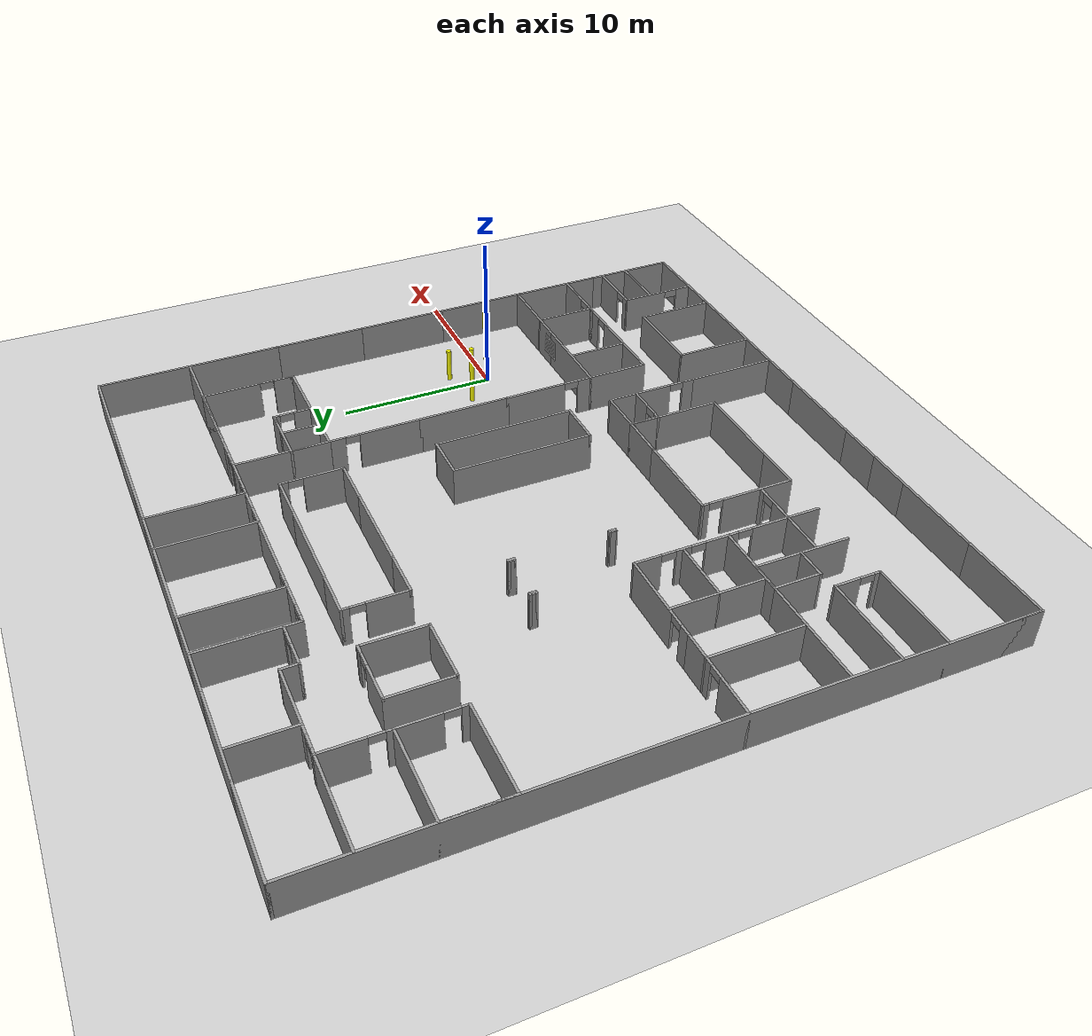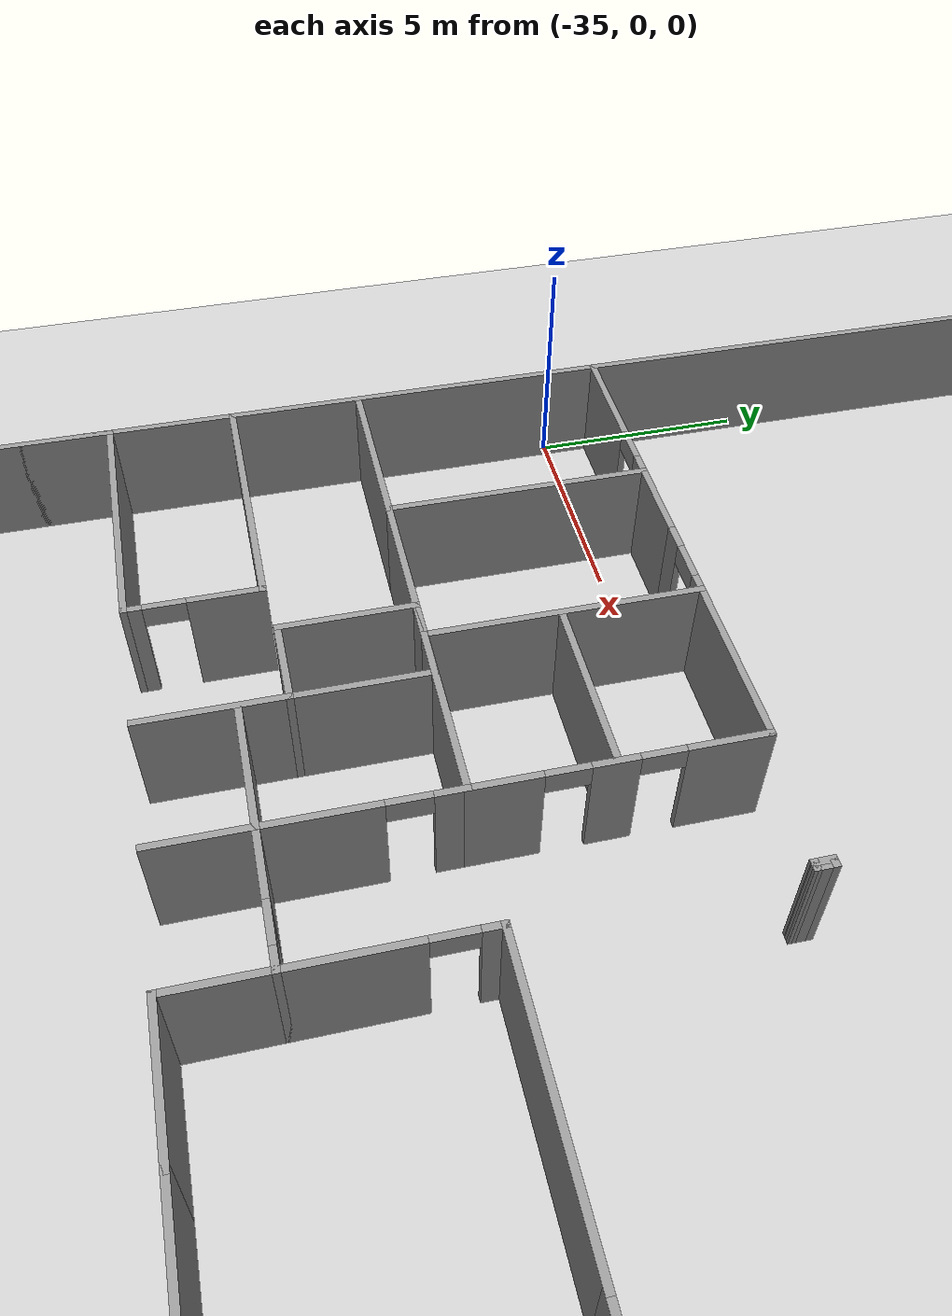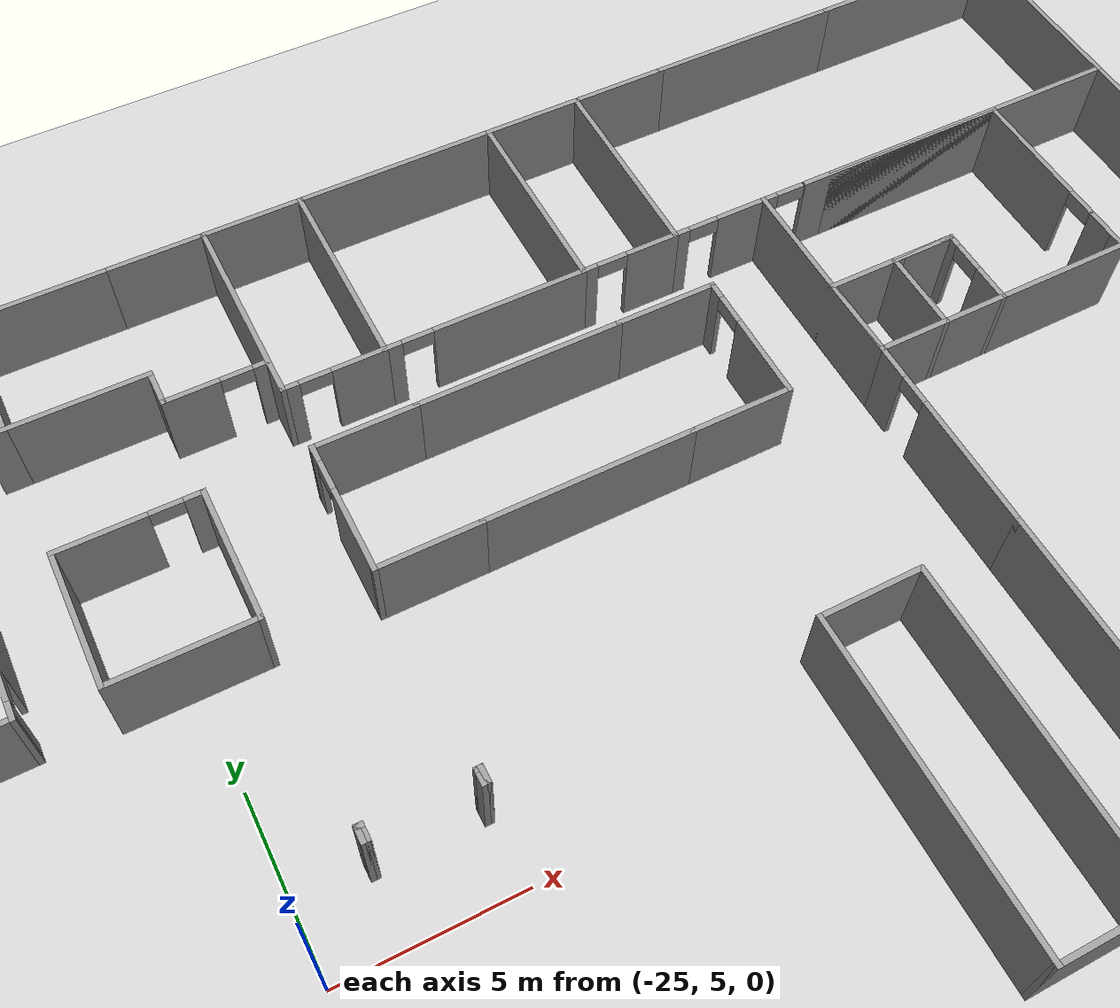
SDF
<sdf version="1.5">
 <world name="default">
  <include><uri>model://sun</uri></include>
  <include><uri>model://ground_plane</uri></include>
  <physics name="default_physics" default="0" type="ode">
   <gravity>0 0 -9.8066</gravity>
   <ode>
    <solver>
     <type>quick</type>
     <iters>10</iters>
     <sor>1.3</sor>
     <use_dynamic_moi_rescaling>0</use_dynamic_moi_rescaling>
    </solver>
    <constraints>
     <cfm>0</cfm>
     <erp>0.2</erp>
     <contact_max_correcting_vel>100</contact_max_correcting_vel>
     <contact_surface_layer>0.001</contact_surface_layer>
    </constraints>
   </ode>
   <max_step_size>0.004</max_step_size>
   <real_time_factor>1</real_time_factor>
   <real_time_update_rate>250</real_time_update_rate>
   <magnetic_field>6.0e-6 2.3e-5 -4.2e-5</magnetic_field>
  </physics>
  <include><name>building</name><pose>-14.5 4 0 0 0 -1.57</pose><uri>model://myhal_V3</uri></include>
  <include>
   <name>checkerboard</name>
   <pose>0 -4.6 1.5 1.57 0 0</pose>
   <uri>model://checkerboard_9_7_0_15</uri>
  </include>
  <include><name>obs1</name><pose>-1.83 1.86 0 0 0 0</pose><uri>model://red_obstacle</uri></include>
  <include><name>obs2</name><pose>1.22 2.3 0 0 0 0</pose><uri>model://green_obstacle</uri></include>
  <include><name>obs3</name><pose>2.54 -0.88 0 0 0 0</pose><uri>model://red_obstacle</uri></include>
 </world>
</sdf>

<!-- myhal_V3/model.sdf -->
<sdf version='1.5'>
  <model name='myhal_V3'>
    <pose frame=''>-2.78092 -0.251424 0 0 -0 0</pose>
    <link name='Wall_319'>
      <collision name='Wall_319_Collision'>
        <geometry>
          <box>
            <size>6 0.15 2.5</size>
          </box>
        </geometry>
        <pose frame=''>0 0 1.25 0 -0 0</pose>
      </collision>
      <visual name='Wall_319_Visual'>
        <pose frame=''>0 0 1.25 0 -0 0</pose>
        <geometry>
          <box>
            <size>6 0.15 2.5</size>
          </box>
        </geometry>
        <material>
          <script>
            <uri>file://media/materials/scripts/gazebo.material</uri>
            <name>Gazebo/Grey</name>
          </script>
          <ambient>1 1 1 1</ambient>
        </material>
        <meta>
          <layer>0</layer>
        </meta>
      </visual>
      <pose frame=''>20.475 17.4 0 0 -0 -1.5708</pose>
    </link>
    <link name='Wall_321'>
      <collision name='Wall_321_Collision'>
        <geometry>
          <box>
            <size>6 0.15 2.5</size>
          </box>
        </geometry>
        <pose frame=''>0 0 1.25 0 -0 0</pose>
      </collision>
      <visual name='Wall_321_Visual'>
        <pose frame=''>0 0 1.25 0 -0 0</pose>
        <geometry>
          <box>
            <size>6 0.15 2.5</size>
          </box>
        </geometry>
        <material>
          <script>
            <uri>file://media/materials/scripts/gazebo.material</uri>
            <name>Gazebo/Grey</name>
          </script>
          <ambient>1 1 1 1</ambient>
        </material>
        <meta>
          <layer>0</layer>
        </meta>
      </visual>
      <pose frame=''>20.475 11.55 0 0 -0 -1.5708</pose>
    </link>
    <link name='Wall_323'>
      <collision name='Wall_323_Collision'>
        <geometry>
          <box>
            <size>3 0.15 2.5</size>
          </box>
        </geometry>
        <pose frame=''>0 0 1.25 0 -0 0</pose>
      </collision>
      <visual name='Wall_323_Visual'>
        <pose frame=''>0 0 1.25 0 -0 0</pose>
        <geometry>
          <box>
            <size>3 0.15 2.5</size>
          </box>
        </geometry>
        <material>
          <script>
            <uri>file://media/materials/scripts/gazebo.material</uri>
            <name>Gazebo/Grey</name>
          </script>
          <ambient>1 1 1 1</ambient>
        </material>
        <meta>
          <layer>0</layer>
        </meta>
      </visual>
      <pose frame=''>20.475 7.2 0 0 -0 -1.5708</pose>
    </link>
    <link name='Wall_324'>
      <collision name='Wall_324_Collision'>
        <geometry>
          <box>
            <size>3 0.15 2.5</size>
          </box>
        </geometry>
        <pose frame=''>0 0 1.25 0 -0 0</pose>
      </collision>
      <visual name='Wall_324_Visual'>
        <pose frame=''>0 0 1.25 0 -0 0</pose>
        <geometry>
          <box>
            <size>3 0.15 2.5</size>
          </box>
        </geometry>
        <material>
          <script>
            <uri>file://media/materials/scripts/gazebo.material</uri>
            <name>Gazebo/Grey</name>
          </script>
          <ambient>1 1 1 1</ambient>
        </material>
        <meta>
          <layer>0</layer>
        </meta>
      </visual>
      <pose frame=''>20.475 4.35 0 0 -0 -1.5708</pose>
    </link>
    <link name='Wall_326'>
      <collision name='Wall_326_Collision'>
        <geometry>
          <box>
            <size>6 0.15 2.5</size>
          </box>
        </geometry>
        <pose frame=''>0 0 1.25 0 -0 0</pose>
      </collision>
      <visual name='Wall_326_Visual'>
        <pose frame=''>0 0 1.25 0 -0 0</pose>
        <geometry>
          <box>
            <size>6 0.15 2.5</size>
          </box>
        </geometry>
        <material>
          <script>
            <uri>file://media/materials/scripts/gazebo.material</uri>
            <name>Gazebo/Grey</name>
          </script>
          <ambient>1 1 1 1</ambient>
        </material>
        <meta>
          <layer>0</layer>
        </meta>
      </visual>
      <pose frame=''>20.475 0 0 0 -0 -1.5708</pose>
    </link>
    <link name='Wall_327'>
      <collision name='Wall_327_Collision'>
        <geometry>
          <box>
            <size>3 0.15 2.5</size>
          </box>
        </geometry>
        <pose frame=''>0 0 1.25 0 -0 0</pose>
      </collision>
      <visual name='Wall_327_Visual'>
        <pose frame=''>0 0 1.25 0 -0 0</pose>
        <geometry>
          <box>
            <size>3 0.15 2.5</size>
          </box>
        </geometry>
        <material>
          <script>
            <uri>file://media/materials/scripts/gazebo.material</uri>
            <name>Gazebo/Grey</name>
          </script>
          <ambient>1 1 1 1</ambient>
        </material>
        <meta>
          <layer>0</layer>
        </meta>
      </visual>
      <pose frame=''>20.475 -4.35 0 0 -0 -1.5708</pose>
    </link>
    <link name='Wall_328'>
      <collision name='Wall_328_Collision'>
        <geometry>
          <box>
            <size>3 0.15 2.5</size>
          </box>
        </geometry>
        <pose frame=''>0 0 1.25 0 -0 0</pose>
      </collision>
      <visual name='Wall_328_Visual'>
        <pose frame=''>0 0 1.25 0 -0 0</pose>
        <geometry>
          <box>
            <size>3 0.15 2.5</size>
          </box>
        </geometry>
        <material>
          <script>
            <uri>file://media/materials/scripts/gazebo.material</uri>
            <name>Gazebo/Grey</name>
          </script>
          <ambient>1 1 1 1</ambient>
        </material>
        <meta>
          <layer>0</layer>
        </meta>
      </visual>
      <pose frame=''>20.475 -7.2 0 0 -0 -1.5708</pose>
    </link>
    <link name='Wall_330'>
      <collision name='Wall_330_Collision'>
        <geometry>
          <box>
            <size>6 0.15 2.5</size>
          </box>
        </geometry>
        <pose frame=''>0 0 1.25 0 -0 0</pose>
      </collision>
      <visual name='Wall_330_Visual'>
        <pose frame=''>0 0 1.25 0 -0 0</pose>
        <geometry>
          <box>
            <size>6 0.15 2.5</size>
          </box>
        </geometry>
        <material>
          <script>
            <uri>file://media/materials/scripts/gazebo.material</uri>
            <name>Gazebo/Grey</name>
          </script>
          <ambient>1 1 1 1</ambient>
        </material>
        <meta>
          <layer>0</layer>
        </meta>
      </visual>
      <pose frame=''>20.475 -11.55 0 0 -0 -1.5708</pose>
    </link>
    <link name='Wall_331'>
      <collision name='Wall_331_Collision'>
        <geometry>
          <box>
            <size>6 0.15 2.5</size>
          </box>
        </geometry>
        <pose frame=''>0 0 1.25 0 -0 0</pose>
      </collision>
      <visual name='Wall_331_Visual'>
        <pose frame=''>0 0 1.25 0 -0 0</pose>
        <geometry>
          <box>
            <size>6 0.15 2.5</size>
          </box>
        </geometry>
        <material>
          <script>
            <uri>file://media/materials/scripts/gazebo.material</uri>
            <name>Gazebo/Grey</name>
          </script>
          <ambient>1 1 1 1</ambient>
        </material>
        <meta>
          <layer>0</layer>
        </meta>
      </visual>
      <pose frame=''>20.475 -17.4 0 0 -0 -1.5708</pose>
    </link>
    <link name='Wall_333'>
      <collision name='Wall_333_Collision'>
        <geometry>
          <box>
            <size>6 0.15 2.5</size>
          </box>
        </geometry>
        <pose frame=''>0 0 1.25 0 -0 0</pose>
      </collision>
      <visual name='Wall_333_Visual'>
        <pose frame=''>0 0 1.25 0 -0 0</pose>
        <geometry>
          <box>
            <size>6 0.15 2.5</size>
          </box>
        </geometry>
        <material>
          <script>
            <uri>file://media/materials/scripts/gazebo.material</uri>
            <name>Gazebo/Grey</name>
          </script>
          <ambient>1 1 1 1</ambient>
        </material>
        <meta>
          <layer>0</layer>
        </meta>
      </visual>
      <pose frame=''>17.55 20.325 0 0 -0 3.14159</pose>
    </link>
    <link name='Wall_334'>
      <collision name='Wall_334_Collision'>
        <geometry>
          <box>
            <size>6 0.15 2.5</size>
          </box>
        </geometry>
        <pose frame=''>0 0 1.25 0 -0 0</pose>
      </collision>
      <visual name='Wall_334_Visual'>
        <pose frame=''>0 0 1.25 0 -0 0</pose>
        <geometry>
          <box>
            <size>6 0.15 2.5</size>
          </box>
        </geometry>
        <material>
          <script>
            <uri>file://media/materials/scripts/gazebo.material</uri>
            <name>Gazebo/Grey</name>
          </script>
          <ambient>1 1 1 1</ambient>
        </material>
        <meta>
          <layer>0</layer>
        </meta>
      </visual>
      <pose frame=''>11.7 20.325 0 0 -0 3.14159</pose>
    </link>
    <link name='Wall_335'>
      <collision name='Wall_335_Collision'>
        <geometry>
          <box>
            <size>6 0.15 2.5</size>
          </box>
        </geometry>
        <pose frame=''>0 0 1.25 0 -0 0</pose>
      </collision>
      <visual name='Wall_335_Visual'>
        <pose frame=''>0 0 1.25 0 -0 0</pose>
        <geometry>
          <box>
            <size>6 0.15 2.5</size>
          </box>
        </geometry>
        <material>
          <script>
            <uri>file://media/materials/scripts/gazebo.material</uri>
            <name>Gazebo/Grey</name>
          </script>
          <ambient>1 1 1 1</ambient>
        </material>
        <meta>
          <layer>0</layer>
        </meta>
      </visual>
      <pose frame=''>5.85 20.325 0 0 -0 3.14159</pose>
    </link>
    <link name='Wall_336'>
      <collision name='Wall_336_Collision'>
        <geometry>
          <box>
            <size>6 0.15 2.5</size>
          </box>
        </geometry>
        <pose frame=''>0 0 1.25 0 -0 0</pose>
      </collision>
      <visual name='Wall_336_Visual'>
        <pose frame=''>0 0 1.25 0 -0 0</pose>
        <geometry>
          <box>
            <size>6 0.15 2.5</size>
          </box>
        </geometry>
        <material>
          <script>
            <uri>file://media/materials/scripts/gazebo.material</uri>
            <name>Gazebo/Grey</name>
          </script>
          <ambient>1 1 1 1</ambient>
        </material>
        <meta>
          <layer>0</layer>
        </meta>
      </visual>
      <pose frame=''>-0 20.325 0 0 -0 3.14159</pose>
    </link>
    <link name='Wall_337'>
      <collision name='Wall_337_Collision'>
        <geometry>
          <box>
            <size>6 0.15 2.5</size>
          </box>
        </geometry>
        <pose frame=''>0 0 1.25 0 -0 0</pose>
      </collision>
      <visual name='Wall_337_Visual'>
        <pose frame=''>0 0 1.25 0 -0 0</pose>
        <geometry>
          <box>
            <size>6 0.15 2.5</size>
          </box>
        </geometry>
        <material>
          <script>
            <uri>file://media/materials/scripts/gazebo.material</uri>
            <name>Gazebo/Grey</name>
          </script>
          <ambient>1 1 1 1</ambient>
        </material>
        <meta>
          <layer>0</layer>
        </meta>
      </visual>
      <pose frame=''>-5.85 20.325 0 0 -0 3.14159</pose>
    </link>
    <link name='Wall_338'>
      <collision name='Wall_338_Collision'>
        <geometry>
          <box>
            <size>6 0.15 2.5</size>
          </box>
        </geometry>
        <pose frame=''>0 0 1.25 0 -0 0</pose>
      </collision>
      <visual name='Wall_338_Visual'>
        <pose frame=''>0 0 1.25 0 -0 0</pose>
        <geometry>
          <box>
            <size>6 0.15 2.5</size>
          </box>
        </geometry>
        <material>
          <script>
            <uri>file://media/materials/scripts/gazebo.material</uri>
            <name>Gazebo/Grey</name>
          </script>
          <ambient>1 1 1 1</ambient>
        </material>
        <meta>
          <layer>0</layer>
        </meta>
      </visual>
      <pose frame=''>-11.7 20.325 0 0 -0 3.14159</pose>
    </link>
    <link name='Wall_339'>
      <collision name='Wall_339_Collision'>
        <geometry>
          <box>
            <size>6 0.15 2.5</size>
          </box>
        </geometry>
        <pose frame=''>0 0 1.25 0 -0 0</pose>
      </collision>
      <visual name='Wall_339_Visual'>
        <pose frame=''>0 0 1.25 0 -0 0</pose>
        <geometry>
          <box>
            <size>6 0.15 2.5</size>
          </box>
        </geometry>
        <material>
          <script>
            <uri>file://media/materials/scripts/gazebo.material</uri>
            <name>Gazebo/Grey</name>
          </script>
          <ambient>1 1 1 1</ambient>
        </material>
        <meta>
          <layer>0</layer>
        </meta>
      </visual>
      <pose frame=''>-17.55 20.325 0 0 -0 3.14159</pose>
    </link>
    <link name='Wall_341'>
      <collision name='Wall_341_Collision'>
        <geometry>
          <box>
            <size>6 0.15 2.5</size>
          </box>
        </geometry>
        <pose frame=''>0 0 1.25 0 -0 0</pose>
      </collision>
      <visual name='Wall_341_Visual'>
        <pose frame=''>0 0 1.25 0 -0 0</pose>
        <geometry>
          <box>
            <size>6 0.15 2.5</size>
          </box>
        </geometry>
        <material>
          <script>
            <uri>file://media/materials/scripts/gazebo.material</uri>
            <name>Gazebo/Grey</name>
          </script>
          <ambient>1 1 1 1</ambient>
        </material>
        <meta>
          <layer>0</layer>
        </meta>
      </visual>
      <pose frame=''>-20.475 17.4 0 0 -0 -1.5708</pose>
    </link>
    <link name='Wall_342'>
      <collision name='Wall_342_Collision'>
        <geometry>
          <box>
            <size>6 0.15 2.5</size>
          </box>
        </geometry>
        <pose frame=''>0 0 1.25 0 -0 0</pose>
      </collision>
      <visual name='Wall_342_Visual'>
        <pose frame=''>0 0 1.25 0 -0 0</pose>
        <geometry>
          <box>
            <size>6 0.15 2.5</size>
          </box>
        </geometry>
        <material>
          <script>
            <uri>file://media/materials/scripts/gazebo.material</uri>
            <name>Gazebo/Grey</name>
          </script>
          <ambient>1 1 1 1</ambient>
        </material>
        <meta>
          <layer>0</layer>
        </meta>
      </visual>
      <pose frame=''>-20.475 11.55 0 0 -0 -1.5708</pose>
    </link>
    <link name='Wall_343'>
      <collision name='Wall_343_Collision'>
        <geometry>
          <box>
            <size>3 0.15 2.5</size>
          </box>
        </geometry>
        <pose frame=''>0 0 1.25 0 -0 0</pose>
      </collision>
      <visual name='Wall_343_Visual'>
        <pose frame=''>0 0 1.25 0 -0 0</pose>
        <geometry>
          <box>
            <size>3 0.15 2.5</size>
          </box>
        </geometry>
        <material>
          <script>
            <uri>file://media/materials/scripts/gazebo.material</uri>
            <name>Gazebo/Grey</name>
          </script>
          <ambient>1 1 1 1</ambient>
        </material>
        <meta>
          <layer>0</layer>
        </meta>
      </visual>
      <pose frame=''>-20.475 7.2 0 0 -0 -1.5708</pose>
    </link>
    <link name='Wall_344'>
      <collision name='Wall_344_Collision'>
        <geometry>
          <box>
            <size>3 0.15 2.5</size>
          </box>
        </geometry>
        <pose frame=''>0 0 1.25 0 -0 0</pose>
      </collision>
      <visual name='Wall_344_Visual'>
        <pose frame=''>0 0 1.25 0 -0 0</pose>
        <geometry>
          <box>
            <size>3 0.15 2.5</size>
          </box>
        </geometry>
        <material>
          <script>
            <uri>file://media/materials/scripts/gazebo.material</uri>
            <name>Gazebo/Grey</name>
          </script>
          <ambient>1 1 1 1</ambient>
        </material>
        <meta>
          <layer>0</layer>
        </meta>
      </visual>
      <pose frame=''>-20.475 4.35 0 0 -0 -1.5708</pose>
    </link>
    <link name='Wall_345'>
      <collision name='Wall_345_Collision'>
        <geometry>
          <box>
            <size>6 0.15 2.5</size>
          </box>
        </geometry>
        <pose frame=''>0 0 1.25 0 -0 0</pose>
      </collision>
      <visual name='Wall_345_Visual'>
        <pose frame=''>0 0 1.25 0 -0 0</pose>
        <geometry>
          <box>
            <size>6 0.15 2.5</size>
          </box>
        </geometry>
        <material>
          <script>
            <uri>file://media/materials/scripts/gazebo.material</uri>
            <name>Gazebo/Grey</name>
          </script>
          <ambient>1 1 1 1</ambient>
        </material>
        <meta>
          <layer>0</layer>
        </meta>
      </visual>
      <pose frame=''>-20.475 0 0 0 -0 -1.5708</pose>
    </link>
    <link name='Wall_347'>
      <collision name='Wall_347_Collision'>
        <geometry>
          <box>
            <size>3 0.15 2.5</size>
          </box>
        </geometry>
        <pose frame=''>0 0 1.25 0 -0 0</pose>
      </collision>
      <visual name='Wall_347_Visual'>
        <pose frame=''>0 0 1.25 0 -0 0</pose>
        <geometry>
          <box>
            <size>3 0.15 2.5</size>
          </box>
        </geometry>
        <material>
          <script>
            <uri>file://media/materials/scripts/gazebo.material</uri>
            <name>Gazebo/Grey</name>
          </script>
          <ambient>1 1 1 1</ambient>
        </material>
        <meta>
          <layer>0</layer>
        </meta>
      </visual>
      <pose frame=''>-20.475 -4.35 0 0 -0 -1.5708</pose>
    </link>
    <link name='Wall_348'>
      <collision name='Wall_348_Collision'>
        <geometry>
          <box>
            <size>3 0.15 2.5</size>
          </box>
        </geometry>
        <pose frame=''>0 0 1.25 0 -0 0</pose>
      </collision>
      <visual name='Wall_348_Visual'>
        <pose frame=''>0 0 1.25 0 -0 0</pose>
        <geometry>
          <box>
            <size>3 0.15 2.5</size>
          </box>
        </geometry>
        <material>
          <script>
            <uri>file://media/materials/scripts/gazebo.material</uri>
            <name>Gazebo/Grey</name>
          </script>
          <ambient>1 1 1 1</ambient>
        </material>
        <meta>
          <layer>0</layer>
        </meta>
      </visual>
      <pose frame=''>-20.475 -7.2 0 0 -0 -1.5708</pose>
    </link>
    <link name='Wall_349'>
      <collision name='Wall_349_Collision'>
        <geometry>
          <box>
            <size>6 0.15 2.5</size>
          </box>
        </geometry>
        <pose frame=''>0 0 1.25 0 -0 0</pose>
      </collision>
      <visual name='Wall_349_Visual'>
        <pose frame=''>0 0 1.25 0 -0 0</pose>
        <geometry>
          <box>
            <size>6 0.15 2.5</size>
          </box>
        </geometry>
        <material>
          <script>
            <uri>file://media/materials/scripts/gazebo.material</uri>
            <name>Gazebo/Grey</name>
          </script>
          <ambient>1 1 1 1</ambient>
        </material>
        <meta>
          <layer>0</layer>
        </meta>
      </visual>
      <pose frame=''>-20.475 -11.55 0 0 -0 -1.5708</pose>
    </link>
    <link name='Wall_351'>
      <collision name='Wall_351_Collision'>
        <geometry>
          <box>
            <size>6 0.15 2.5</size>
          </box>
        </geometry>
        <pose frame=''>0 0 1.25 0 -0 0</pose>
      </collision>
      <visual name='Wall_351_Visual'>
        <pose frame=''>0 0 1.25 0 -0 0</pose>
        <geometry>
          <box>
            <size>6 0.15 2.5</size>
          </box>
        </geometry>
        <material>
          <script>
            <uri>file://media/materials/scripts/gazebo.material</uri>
            <name>Gazebo/Grey</name>
          </script>
          <ambient>1 1 1 1</ambient>
        </material>
        <meta>
          <layer>0</layer>
        </meta>
      </visual>
      <pose frame=''>-20.475 -17.4 0 0 -0 -1.5708</pose>
    </link>
    <link name='Wall_352'>
      <collision name='Wall_352_Collision'>
        <geometry>
          <box>
            <size>41 0.15 2.5</size>
          </box>
        </geometry>
        <pose frame=''>0 0 1.25 0 -0 0</pose>
      </collision>
      <visual name='Wall_352_Visual'>
        <pose frame=''>0 0 1.25 0 -0 0</pose>
        <geometry>
          <box>
            <size>41 0.15 2.5</size>
          </box>
        </geometry>
        <material>
          <script>
            <uri>file://media/materials/scripts/gazebo.material</uri>
            <name>Gazebo/Grey</name>
          </script>
          <ambient>1 1 1 1</ambient>
        </material>
        <meta>
          <layer>0</layer>
        </meta>
      </visual>
      <pose frame=''>-0.05 -20.325 0 0 -0 0</pose>
    </link>
    <link name='Wall_358'>
      <collision name='Wall_358_Collision'>
        <geometry>
          <box>
            <size>4 0.15 2.5</size>
          </box>
        </geometry>
        <pose frame=''>0 0 1.25 0 -0 0</pose>
      </collision>
      <visual name='Wall_358_Visual'>
        <pose frame=''>0 0 1.25 0 -0 0</pose>
        <geometry>
          <box>
            <size>4 0.15 2.5</size>
          </box>
        </geometry>
        <material>
          <script>
            <uri>file://media/materials/scripts/gazebo.material</uri>
            <name>Gazebo/Grey</name>
          </script>
          <ambient>1 1 1 1</ambient>
        </material>
        <meta>
          <layer>0</layer>
        </meta>
      </visual>
      <pose frame=''>-14.625 18.4 0 0 -0 1.5708</pose>
    </link>
    <link name='Wall_360'>
      <pose frame=''>-11.7 16.475 0 0 -0 0</pose>
      <visual name='Wall_360_Visual_0'>
        <pose frame=''>-1.13429 0 1.25 0 -0 0</pose>
        <geometry>
          <box>
            <size>3.73142 0.15 2.5</size>
          </box>
        </geometry>
        <material>
          <script>
            <uri>file://media/materials/scripts/gazebo.material</uri>
            <name>Gazebo/Grey</name>
          </script>
          <ambient>1 1 1 1</ambient>
        </material>
        <meta>
          <layer>0</layer>
        </meta>
      </visual>
      <collision name='Wall_360_Collision_0'>
        <geometry>
          <box>
            <size>3.73142 0.15 2.5</size>
          </box>
        </geometry>
        <pose frame=''>-1.13429 0 1.25 0 -0 0</pose>
      </collision>
      <visual name='Wall_360_Visual_1'>
        <pose frame=''>2.31571 0 1.25 0 -0 0</pose>
        <geometry>
          <box>
            <size>1.36858 0.15 2.5</size>
          </box>
        </geometry>
        <material>
          <script>
            <uri>file://media/materials/scripts/gazebo.material</uri>
            <name>Gazebo/Grey</name>
          </script>
          <ambient>1 1 1 1</ambient>
        </material>
        <meta>
          <layer>0</layer>
        </meta>
      </visual>
      <collision name='Wall_360_Collision_1'>
        <geometry>
          <box>
            <size>1.36858 0.15 2.5</size>
          </box>
        </geometry>
        <pose frame=''>2.31571 0 1.25 0 -0 0</pose>
      </collision>
      <visual name='Wall_360_Visual_2'>
        <pose frame=''>2.74704 0 1.25 0 -0 0</pose>
        <geometry>
          <box>
            <size>0.505924 0.15 2.5</size>
          </box>
        </geometry>
        <material>
          <script>
            <uri>file://media/materials/scripts/gazebo.material</uri>
            <name>Gazebo/Grey</name>
          </script>
          <ambient>1 1 1 1</ambient>
        </material>
        <meta>
          <layer>0</layer>
        </meta>
      </visual>
      <collision name='Wall_360_Collision_2'>
        <geometry>
          <box>
            <size>0.505924 0.15 2.5</size>
          </box>
        </geometry>
        <pose frame=''>2.74704 0 1.25 0 -0 0</pose>
      </collision>
      <visual name='Wall_360_Visual_3'>
        <pose frame=''>1.16275 0 2.25 0 -0 0</pose>
        <geometry>
          <box>
            <size>0.862653 0.15 0.5</size>
          </box>
        </geometry>
        <material>
          <script>
            <uri>file://media/materials/scripts/gazebo.material</uri>
            <name>Gazebo/Grey</name>
          </script>
          <ambient>1 1 1 1</ambient>
        </material>
        <meta>
          <layer>0</layer>
        </meta>
      </visual>
      <collision name='Wall_360_Collision_3'>
        <geometry>
          <box>
            <size>0.862653 0.15 0.5</size>
          </box>
        </geometry>
        <pose frame=''>1.16275 0 2.25 0 -0 0</pose>
      </collision>
    </link>
    <link name='Wall_362'>
      <collision name='Wall_362_Collision'>
        <geometry>
          <box>
            <size>8 0.15 2.5</size>
          </box>
        </geometry>
        <pose frame=''>0 0 1.25 0 -0 0</pose>
      </collision>
      <visual name='Wall_362_Visual'>
        <pose frame=''>0 0 1.25 0 -0 0</pose>
        <geometry>
          <box>
            <size>8 0.15 2.5</size>
          </box>
        </geometry>
        <material>
          <script>
            <uri>file://media/materials/scripts/gazebo.material</uri>
            <name>Gazebo/Grey</name>
          </script>
          <ambient>1 1 1 1</ambient>
        </material>
        <meta>
          <layer>0</layer>
        </meta>
      </visual>
      <pose frame=''>-8.775 12.55 0 0 -0 -1.5708</pose>
    </link>
    <link name='Wall_363'>
      <collision name='Wall_363_Collision'>
        <geometry>
          <box>
            <size>6 0.15 2.5</size>
          </box>
        </geometry>
        <pose frame=''>0 0 1.25 0 -0 0</pose>
      </collision>
      <visual name='Wall_363_Visual'>
        <pose frame=''>0 0 1.25 0 -0 0</pose>
        <geometry>
          <box>
            <size>6 0.15 2.5</size>
          </box>
        </geometry>
        <material>
          <script>
            <uri>file://media/materials/scripts/gazebo.material</uri>
            <name>Gazebo/Grey</name>
          </script>
          <ambient>1 1 1 1</ambient>
        </material>
        <meta>
          <layer>0</layer>
        </meta>
      </visual>
      <pose frame=''>-11.7 8.625 0 0 -0 3.14159</pose>
    </link>
    <link name='Wall_364'>
      <pose frame=''>-14.625 12.55 0 0 -0 1.5708</pose>
      <visual name='Wall_364_Visual_0'>
        <pose frame=''>-3.75018 0 1.25 0 -0 0</pose>
        <geometry>
          <box>
            <size>0.499636 0.15 2.5</size>
          </box>
        </geometry>
        <material>
          <script>
            <uri>file://media/materials/scripts/gazebo.material</uri>
            <name>Gazebo/Grey</name>
          </script>
          <ambient>1 1 1 1</ambient>
        </material>
        <meta>
          <layer>0</layer>
        </meta>
      </visual>
      <collision name='Wall_364_Collision_0'>
        <geometry>
          <box>
            <size>0.499636 0.15 2.5</size>
          </box>
        </geometry>
        <pose frame=''>-3.75018 0 1.25 0 -0 0</pose>
      </collision>
      <visual name='Wall_364_Visual_1'>
        <pose frame=''>0.699818 0 1.25 0 -0 0</pose>
        <geometry>
          <box>
            <size>6.60036 0.15 2.5</size>
          </box>
        </geometry>
        <material>
          <script>
            <uri>file://media/materials/scripts/gazebo.material</uri>
            <name>Gazebo/Grey</name>
          </script>
          <ambient>1 1 1 1</ambient>
        </material>
        <meta>
          <layer>0</layer>
        </meta>
      </visual>
      <collision name='Wall_364_Collision_1'>
        <geometry>
          <box>
            <size>6.60036 0.15 2.5</size>
          </box>
        </geometry>
        <pose frame=''>0.699818 0 1.25 0 -0 0</pose>
      </collision>
      <visual name='Wall_364_Visual_2'>
        <pose frame=''>1.13114 0 1.25 0 -0 0</pose>
        <geometry>
          <box>
            <size>5.73771 0.15 2.5</size>
          </box>
        </geometry>
        <material>
          <script>
            <uri>file://media/materials/scripts/gazebo.material</uri>
            <name>Gazebo/Grey</name>
          </script>
          <ambient>1 1 1 1</ambient>
        </material>
        <meta>
          <layer>0</layer>
        </meta>
      </visual>
      <collision name='Wall_364_Collision_2'>
        <geometry>
          <box>
            <size>5.73771 0.15 2.5</size>
          </box>
        </geometry>
        <pose frame=''>1.13114 0 1.25 0 -0 0</pose>
      </collision>
      <visual name='Wall_364_Visual_3'>
        <pose frame=''>-3.06904 0 2.25 0 -0 0</pose>
        <geometry>
          <box>
            <size>0.862653 0.15 0.5</size>
          </box>
        </geometry>
        <material>
          <script>
            <uri>file://media/materials/scripts/gazebo.material</uri>
            <name>Gazebo/Grey</name>
          </script>
          <ambient>1 1 1 1</ambient>
        </material>
        <meta>
          <layer>0</layer>
        </meta>
      </visual>
      <collision name='Wall_364_Collision_3'>
        <geometry>
          <box>
            <size>0.862653 0.15 0.5</size>
          </box>
        </geometry>
        <pose frame=''>-3.06904 0 2.25 0 -0 0</pose>
      </collision>
    </link>
    <link name='Wall_366'>
      <collision name='Wall_366_Collision'>
        <geometry>
          <box>
            <size>2.5 0.15 2.5</size>
          </box>
        </geometry>
        <pose frame=''>0 0 1.25 0 -0 0</pose>
      </collision>
      <visual name='Wall_366_Visual'>
        <pose frame=''>0 0 1.25 0 -0 0</pose>
        <geometry>
          <box>
            <size>2.5 0.15 2.5</size>
          </box>
        </geometry>
        <material>
          <script>
            <uri>file://media/materials/scripts/gazebo.material</uri>
            <name>Gazebo/Grey</name>
          </script>
          <ambient>1 1 1 1</ambient>
        </material>
        <meta>
          <layer>0</layer>
        </meta>
      </visual>
      <pose frame=''>-9.95 8.625 0 0 -0 3.14159</pose>
    </link>
    <link name='Wall_367'>
      <collision name='Wall_367_Collision'>
        <geometry>
          <box>
            <size>4 0.15 2.5</size>
          </box>
        </geometry>
        <pose frame=''>0 0 1.25 0 -0 0</pose>
      </collision>
      <visual name='Wall_367_Visual'>
        <pose frame=''>0 0 1.25 0 -0 0</pose>
        <geometry>
          <box>
            <size>4 0.15 2.5</size>
          </box>
        </geometry>
        <material>
          <script>
            <uri>file://media/materials/scripts/gazebo.material</uri>
            <name>Gazebo/Grey</name>
          </script>
          <ambient>1 1 1 1</ambient>
        </material>
        <meta>
          <layer>0</layer>
        </meta>
      </visual>
      <pose frame=''>-11.125 10.55 0 0 -0 1.5708</pose>
    </link>
    <link name='Wall_368'>
      <pose frame=''>-9.95 12.475 0 0 -0 0</pose>
      <visual name='Wall_368_Visual_0'>
        <pose frame=''>-1.03753 0 1.25 0 -0 0</pose>
        <geometry>
          <box>
            <size>0.424942 0.15 2.5</size>
          </box>
        </geometry>
        <material>
          <script>
            <uri>file://media/materials/scripts/gazebo.material</uri>
            <name>Gazebo/Grey</name>
          </script>
          <ambient>1 1 1 1</ambient>
        </material>
        <meta>
          <layer>0</layer>
        </meta>
      </visual>
      <collision name='Wall_368_Collision_0'>
        <geometry>
          <box>
            <size>0.424942 0.15 2.5</size>
          </box>
        </geometry>
        <pose frame=''>-1.03753 0 1.25 0 -0 0</pose>
      </collision>
      <visual name='Wall_368_Visual_1'>
        <pose frame=''>0.662471 0 1.25 0 -0 0</pose>
        <geometry>
          <box>
            <size>1.17506 0.15 2.5</size>
          </box>
        </geometry>
        <material>
          <script>
            <uri>file://media/materials/scripts/gazebo.material</uri>
            <name>Gazebo/Grey</name>
          </script>
          <ambient>1 1 1 1</ambient>
        </material>
        <meta>
          <layer>0</layer>
        </meta>
      </visual>
      <collision name='Wall_368_Collision_1'>
        <geometry>
          <box>
            <size>1.17506 0.15 2.5</size>
          </box>
        </geometry>
        <pose frame=''>0.662471 0 1.25 0 -0 0</pose>
      </collision>
      <visual name='Wall_368_Visual_2'>
        <pose frame=''>-0.375058 0 2.25 0 -0 0</pose>
        <geometry>
          <box>
            <size>0.9 0.15 0.5</size>
          </box>
        </geometry>
        <material>
          <script>
            <uri>file://media/materials/scripts/gazebo.material</uri>
            <name>Gazebo/Grey</name>
          </script>
          <ambient>1 1 1 1</ambient>
        </material>
        <meta>
          <layer>0</layer>
        </meta>
      </visual>
      <collision name='Wall_368_Collision_2'>
        <geometry>
          <box>
            <size>0.9 0.15 0.5</size>
          </box>
        </geometry>
        <pose frame=''>-0.375058 0 2.25 0 -0 0</pose>
      </collision>
    </link>
    <link name='Wall_370'>
      <pose frame=''>-5.85 8.625 0 0 -0 0</pose>
      <visual name='Wall_370_Visual_0'>
        <pose frame=''>-2.45569 0 1.25 0 -0 0</pose>
        <geometry>
          <box>
            <size>1.08861 0.15 2.5</size>
          </box>
        </geometry>
        <material>
          <script>
            <uri>file://media/materials/scripts/gazebo.material</uri>
            <name>Gazebo/Grey</name>
          </script>
          <ambient>1 1 1 1</ambient>
        </material>
        <meta>
          <layer>0</layer>
        </meta>
      </visual>
      <collision name='Wall_370_Collision_0'>
        <geometry>
          <box>
            <size>1.08861 0.15 2.5</size>
          </box>
        </geometry>
        <pose frame=''>-2.45569 0 1.25 0 -0 0</pose>
      </collision>
      <visual name='Wall_370_Visual_1'>
        <pose frame=''>0.994306 0 1.25 0 -0 0</pose>
        <geometry>
          <box>
            <size>4.01139 0.15 2.5</size>
          </box>
        </geometry>
        <material>
          <script>
            <uri>file://media/materials/scripts/gazebo.material</uri>
            <name>Gazebo/Grey</name>
          </script>
          <ambient>1 1 1 1</ambient>
        </material>
        <meta>
          <layer>0</layer>
        </meta>
      </visual>
      <collision name='Wall_370_Collision_1'>
        <geometry>
          <box>
            <size>4.01139 0.15 2.5</size>
          </box>
        </geometry>
        <pose frame=''>0.994306 0 1.25 0 -0 0</pose>
      </collision>
      <visual name='Wall_370_Visual_2'>
        <pose frame=''>-1.46139 0 2.25 0 -0 0</pose>
        <geometry>
          <box>
            <size>0.9 0.15 0.5</size>
          </box>
        </geometry>
        <material>
          <script>
            <uri>file://media/materials/scripts/gazebo.material</uri>
            <name>Gazebo/Grey</name>
          </script>
          <ambient>1 1 1 1</ambient>
        </material>
        <meta>
          <layer>0</layer>
        </meta>
      </visual>
      <collision name='Wall_370_Collision_2'>
        <geometry>
          <box>
            <size>0.9 0.15 0.5</size>
          </box>
        </geometry>
        <pose frame=''>-1.46139 0 2.25 0 -0 0</pose>
      </collision>
    </link>
    <link name='Wall_371'>
      <collision name='Wall_371_Collision'>
        <geometry>
          <box>
            <size>6 0.15 2.5</size>
          </box>
        </geometry>
        <pose frame=''>0 0 1.25 0 -0 0</pose>
      </collision>
      <visual name='Wall_371_Visual'>
        <pose frame=''>0 0 1.25 0 -0 0</pose>
        <geometry>
          <box>
            <size>6 0.15 2.5</size>
          </box>
        </geometry>
        <material>
          <script>
            <uri>file://media/materials/scripts/gazebo.material</uri>
            <name>Gazebo/Grey</name>
          </script>
          <ambient>1 1 1 1</ambient>
        </material>
        <meta>
          <layer>0</layer>
        </meta>
      </visual>
      <pose frame=''>-0 8.625 0 0 -0 0</pose>
    </link>
    <link name='Wall_372'>
      <pose frame=''>5.85 8.625 0 0 -0 0</pose>
      <visual name='Wall_372_Visual_0'>
        <pose frame=''>-0.95746 0 1.25 0 -0 0</pose>
        <geometry>
          <box>
            <size>4.08508 0.15 2.5</size>
          </box>
        </geometry>
        <material>
          <script>
            <uri>file://media/materials/scripts/gazebo.material</uri>
            <name>Gazebo/Grey</name>
          </script>
          <ambient>1 1 1 1</ambient>
        </material>
        <meta>
          <layer>0</layer>
        </meta>
      </visual>
      <collision name='Wall_372_Collision_0'>
        <geometry>
          <box>
            <size>4.08508 0.15 2.5</size>
          </box>
        </geometry>
        <pose frame=''>-0.95746 0 1.25 0 -0 0</pose>
      </collision>
      <visual name='Wall_372_Visual_1'>
        <pose frame=''>2.49254 0 1.25 0 -0 0</pose>
        <geometry>
          <box>
            <size>1.01492 0.15 2.5</size>
          </box>
        </geometry>
        <material>
          <script>
            <uri>file://media/materials/scripts/gazebo.material</uri>
            <name>Gazebo/Grey</name>
          </script>
          <ambient>1 1 1 1</ambient>
        </material>
        <meta>
          <layer>0</layer>
        </meta>
      </visual>
      <collision name='Wall_372_Collision_1'>
        <geometry>
          <box>
            <size>1.01492 0.15 2.5</size>
          </box>
        </geometry>
        <pose frame=''>2.49254 0 1.25 0 -0 0</pose>
      </collision>
      <visual name='Wall_372_Visual_2'>
        <pose frame=''>1.53508 0 2.25 0 -0 0</pose>
        <geometry>
          <box>
            <size>0.9 0.15 0.5</size>
          </box>
        </geometry>
        <material>
          <script>
            <uri>file://media/materials/scripts/gazebo.material</uri>
            <name>Gazebo/Grey</name>
          </script>
          <ambient>1 1 1 1</ambient>
        </material>
        <meta>
          <layer>0</layer>
        </meta>
      </visual>
      <collision name='Wall_372_Collision_2'>
        <geometry>
          <box>
            <size>0.9 0.15 0.5</size>
          </box>
        </geometry>
        <pose frame=''>1.53508 0 2.25 0 -0 0</pose>
      </collision>
    </link>
    <link name='Wall_373'>
      <collision name='Wall_373_Collision'>
        <geometry>
          <box>
            <size>6 0.15 2.5</size>
          </box>
        </geometry>
        <pose frame=''>0 0 1.25 0 -0 0</pose>
      </collision>
      <visual name='Wall_373_Visual'>
        <pose frame=''>0 0 1.25 0 -0 0</pose>
        <geometry>
          <box>
            <size>6 0.15 2.5</size>
          </box>
        </geometry>
        <material>
          <script>
            <uri>file://media/materials/scripts/gazebo.material</uri>
            <name>Gazebo/Grey</name>
          </script>
          <ambient>1 1 1 1</ambient>
        </material>
        <meta>
          <layer>0</layer>
        </meta>
      </visual>
      <pose frame=''>8.775 11.55 0 0 -0 1.5708</pose>
    </link>
    <link name='Wall_374'>
      <collision name='Wall_374_Collision'>
        <geometry>
          <box>
            <size>6 0.15 2.5</size>
          </box>
        </geometry>
        <pose frame=''>0 0 1.25 0 -0 0</pose>
      </collision>
      <visual name='Wall_374_Visual'>
        <pose frame=''>0 0 1.25 0 -0 0</pose>
        <geometry>
          <box>
            <size>6 0.15 2.5</size>
          </box>
        </geometry>
        <material>
          <script>
            <uri>file://media/materials/scripts/gazebo.material</uri>
            <name>Gazebo/Grey</name>
          </script>
          <ambient>1 1 1 1</ambient>
        </material>
        <meta>
          <layer>0</layer>
        </meta>
      </visual>
      <pose frame=''>8.775 17.4 0 0 -0 1.5708</pose>
    </link>
    <link name='Wall_376'>
      <collision name='Wall_376_Collision'>
        <geometry>
          <box>
            <size>4 0.15 2.5</size>
          </box>
        </geometry>
        <pose frame=''>0 0 1.25 0 -0 0</pose>
      </collision>
      <visual name='Wall_376_Visual'>
        <pose frame=''>0 0 1.25 0 -0 0</pose>
        <geometry>
          <box>
            <size>4 0.15 2.5</size>
          </box>
        </geometry>
        <material>
          <script>
            <uri>file://media/materials/scripts/gazebo.material</uri>
            <name>Gazebo/Grey</name>
          </script>
          <ambient>1 1 1 1</ambient>
        </material>
        <meta>
          <layer>0</layer>
        </meta>
      </visual>
      <pose frame=''>10.7 8.625 0 0 -0 0</pose>
    </link>
    <link name='Wall_377'>
      <pose frame=''>12.625 12.55 0 0 -0 1.5708</pose>
      <visual name='Wall_377_Visual_0'>
        <pose frame=''>-1.16536 0 1.25 0 -0 0</pose>
        <geometry>
          <box>
            <size>5.66928 0.15 2.5</size>
          </box>
        </geometry>
        <material>
          <script>
            <uri>file://media/materials/scripts/gazebo.material</uri>
            <name>Gazebo/Grey</name>
          </script>
          <ambient>1 1 1 1</ambient>
        </material>
        <meta>
          <layer>0</layer>
        </meta>
      </visual>
      <collision name='Wall_377_Collision_0'>
        <geometry>
          <box>
            <size>5.66928 0.15 2.5</size>
          </box>
        </geometry>
        <pose frame=''>-1.16536 0 1.25 0 -0 0</pose>
      </collision>
      <visual name='Wall_377_Visual_1'>
        <pose frame=''>3.28464 0 1.25 0 -0 0</pose>
        <geometry>
          <box>
            <size>1.43072 0.15 2.5</size>
          </box>
        </geometry>
        <material>
          <script>
            <uri>file://media/materials/scripts/gazebo.material</uri>
            <name>Gazebo/Grey</name>
          </script>
          <ambient>1 1 1 1</ambient>
        </material>
        <meta>
          <layer>0</layer>
        </meta>
      </visual>
      <collision name='Wall_377_Collision_1'>
        <geometry>
          <box>
            <size>1.43072 0.15 2.5</size>
          </box>
        </geometry>
        <pose frame=''>3.28464 0 1.25 0 -0 0</pose>
      </collision>
      <visual name='Wall_377_Visual_2'>
        <pose frame=''>3.72381 0 1.25 0 -0 0</pose>
        <geometry>
          <box>
            <size>0.552386 0.15 2.5</size>
          </box>
        </geometry>
        <material>
          <script>
            <uri>file://media/materials/scripts/gazebo.material</uri>
            <name>Gazebo/Grey</name>
          </script>
          <ambient>1 1 1 1</ambient>
        </material>
        <meta>
          <layer>0</layer>
        </meta>
      </visual>
      <collision name='Wall_377_Collision_2'>
        <geometry>
          <box>
            <size>0.552386 0.15 2.5</size>
          </box>
        </geometry>
        <pose frame=''>3.72381 0 1.25 0 -0 0</pose>
      </collision>
      <visual name='Wall_377_Visual_3'>
        <pose frame=''>2.10845 0 2.25 0 -0 0</pose>
        <geometry>
          <box>
            <size>0.878338 0.15 0.5</size>
          </box>
        </geometry>
        <material>
          <script>
            <uri>file://media/materials/scripts/gazebo.material</uri>
            <name>Gazebo/Grey</name>
          </script>
          <ambient>1 1 1 1</ambient>
        </material>
        <meta>
          <layer>0</layer>
        </meta>
      </visual>
      <collision name='Wall_377_Collision_3'>
        <geometry>
          <box>
            <size>0.878338 0.15 0.5</size>
          </box>
        </geometry>
        <pose frame=''>2.10845 0 2.25 0 -0 0</pose>
      </collision>
    </link>
    <link name='Wall_378'>
      <pose frame=''>12.625 18.4 0 0 -0 1.5708</pose>
      <visual name='Wall_378_Visual_0'>
        <pose frame=''>-1.73364 0 1.25 0 -0 0</pose>
        <geometry>
          <box>
            <size>0.532712 0.15 2.5</size>
          </box>
        </geometry>
        <material>
          <script>
            <uri>file://media/materials/scripts/gazebo.material</uri>
            <name>Gazebo/Grey</name>
          </script>
          <ambient>1 1 1 1</ambient>
        </material>
        <meta>
          <layer>0</layer>
        </meta>
      </visual>
      <collision name='Wall_378_Collision_0'>
        <geometry>
          <box>
            <size>0.532712 0.15 2.5</size>
          </box>
        </geometry>
        <pose frame=''>-1.73364 0 1.25 0 -0 0</pose>
      </collision>
      <visual name='Wall_378_Visual_1'>
        <pose frame=''>0.716356 0 1.25 0 -0 0</pose>
        <geometry>
          <box>
            <size>2.56729 0.15 2.5</size>
          </box>
        </geometry>
        <material>
          <script>
            <uri>file://media/materials/scripts/gazebo.material</uri>
            <name>Gazebo/Grey</name>
          </script>
          <ambient>1 1 1 1</ambient>
        </material>
        <meta>
          <layer>0</layer>
        </meta>
      </visual>
      <collision name='Wall_378_Collision_1'>
        <geometry>
          <box>
            <size>2.56729 0.15 2.5</size>
          </box>
        </geometry>
        <pose frame=''>0.716356 0 1.25 0 -0 0</pose>
      </collision>
      <visual name='Wall_378_Visual_2'>
        <pose frame=''>-1.01729 0 2.25 0 -0 0</pose>
        <geometry>
          <box>
            <size>0.9 0.15 0.5</size>
          </box>
        </geometry>
        <material>
          <script>
            <uri>file://media/materials/scripts/gazebo.material</uri>
            <name>Gazebo/Grey</name>
          </script>
          <ambient>1 1 1 1</ambient>
        </material>
        <meta>
          <layer>0</layer>
        </meta>
      </visual>
      <collision name='Wall_378_Collision_2'>
        <geometry>
          <box>
            <size>0.9 0.15 0.5</size>
          </box>
        </geometry>
        <pose frame=''>-1.01729 0 2.25 0 -0 0</pose>
      </collision>
    </link>
    <link name='Wall_380'>
      <collision name='Wall_380_Collision'>
        <geometry>
          <box>
            <size>4 0.15 2.5</size>
          </box>
        </geometry>
        <pose frame=''>0 0 1.25 0 -0 0</pose>
      </collision>
      <visual name='Wall_380_Visual'>
        <pose frame=''>0 0 1.25 0 -0 0</pose>
        <geometry>
          <box>
            <size>4 0.15 2.5</size>
          </box>
        </geometry>
        <material>
          <script>
            <uri>file://media/materials/scripts/gazebo.material</uri>
            <name>Gazebo/Grey</name>
          </script>
          <ambient>1 1 1 1</ambient>
        </material>
        <meta>
          <layer>0</layer>
        </meta>
      </visual>
      <pose frame=''>10.7 16.475 0 0 -0 3.14159</pose>
    </link>
    <link name='Wall_389'>
      <collision name='Wall_389_Collision'>
        <geometry>
          <box>
            <size>5.15 0.15 2.5</size>
          </box>
        </geometry>
        <pose frame=''>0 0 1.25 0 -0 0</pose>
      </collision>
      <visual name='Wall_389_Visual'>
        <pose frame=''>0 0 1.25 0 -0 0</pose>
        <geometry>
          <box>
            <size>5.15 0.15 2.5</size>
          </box>
        </geometry>
        <material>
          <script>
            <uri>file://media/materials/scripts/gazebo.material</uri>
            <name>Gazebo/Grey</name>
          </script>
          <ambient>1 1 1 1</ambient>
        </material>
        <meta>
          <layer>0</layer>
        </meta>
      </visual>
      <pose frame=''>17.975 8.625 0 0 -0 0</pose>
    </link>
    <link name='Wall_392'>
      <pose frame=''>17.9 16.4907 0 0 -0 -0.006468</pose>
      <visual name='Wall_392_Visual_0'>
        <pose frame=''>-0.960517 0 1.25 0 -0 0</pose>
        <geometry>
          <box>
            <size>3.07897 0.15 2.5</size>
          </box>
        </geometry>
        <material>
          <script>
            <uri>file://media/materials/scripts/gazebo.material</uri>
            <name>Gazebo/Grey</name>
          </script>
          <ambient>1 1 1 1</ambient>
        </material>
        <meta>
          <layer>0</layer>
        </meta>
      </visual>
      <collision name='Wall_392_Collision_0'>
        <geometry>
          <box>
            <size>3.07897 0.15 2.5</size>
          </box>
        </geometry>
        <pose frame=''>-0.960517 0 1.25 0 -0 0</pose>
      </collision>
      <visual name='Wall_392_Visual_1'>
        <pose frame=''>1.98948 0 1.25 0 -0 0</pose>
        <geometry>
          <box>
            <size>1.02103 0.15 2.5</size>
          </box>
        </geometry>
        <material>
          <script>
            <uri>file://media/materials/scripts/gazebo.material</uri>
            <name>Gazebo/Grey</name>
          </script>
          <ambient>1 1 1 1</ambient>
        </material>
        <meta>
          <layer>0</layer>
        </meta>
      </visual>
      <collision name='Wall_392_Collision_1'>
        <geometry>
          <box>
            <size>1.02103 0.15 2.5</size>
          </box>
        </geometry>
        <pose frame=''>1.98948 0 1.25 0 -0 0</pose>
      </collision>
      <visual name='Wall_392_Visual_2'>
        <pose frame=''>1.02897 0 2.25 0 -0 0</pose>
        <geometry>
          <box>
            <size>0.9 0.15 0.5</size>
          </box>
        </geometry>
        <material>
          <script>
            <uri>file://media/materials/scripts/gazebo.material</uri>
            <name>Gazebo/Grey</name>
          </script>
          <ambient>1 1 1 1</ambient>
        </material>
        <meta>
          <layer>0</layer>
        </meta>
      </visual>
      <collision name='Wall_392_Collision_2'>
        <geometry>
          <box>
            <size>0.9 0.15 0.5</size>
          </box>
        </geometry>
        <pose frame=''>1.02897 0 2.25 0 -0 0</pose>
      </collision>
    </link>
    <link name='Wall_394'>
      <pose frame=''>15.475 18.4157 0 0 -0 1.5708</pose>
      <visual name='Wall_394_Visual_0'>
        <pose frame=''>-1.73721 0 1.25 0 -0 0</pose>
        <geometry>
          <box>
            <size>0.494202 0.15 2.5</size>
          </box>
        </geometry>
        <material>
          <script>
            <uri>file://media/materials/scripts/gazebo.material</uri>
            <name>Gazebo/Grey</name>
          </script>
          <ambient>1 1 1 1</ambient>
        </material>
        <meta>
          <layer>0</layer>
        </meta>
      </visual>
      <collision name='Wall_394_Collision_0'>
        <geometry>
          <box>
            <size>0.494202 0.15 2.5</size>
          </box>
        </geometry>
        <pose frame=''>-1.73721 0 1.25 0 -0 0</pose>
      </collision>
      <visual name='Wall_394_Visual_1'>
        <pose frame=''>0.697101 0 1.25 0 -0 0</pose>
        <geometry>
          <box>
            <size>2.57443 0.15 2.5</size>
          </box>
        </geometry>
        <material>
          <script>
            <uri>file://media/materials/scripts/gazebo.material</uri>
            <name>Gazebo/Grey</name>
          </script>
          <ambient>1 1 1 1</ambient>
        </material>
        <meta>
          <layer>0</layer>
        </meta>
      </visual>
      <collision name='Wall_394_Collision_1'>
        <geometry>
          <box>
            <size>2.57443 0.15 2.5</size>
          </box>
        </geometry>
        <pose frame=''>0.697101 0 1.25 0 -0 0</pose>
      </collision>
      <visual name='Wall_394_Visual_2'>
        <pose frame=''>-1.04011 0 2.25 0 -0 0</pose>
        <geometry>
          <box>
            <size>0.9 0.15 0.5</size>
          </box>
        </geometry>
        <material>
          <script>
            <uri>file://media/materials/scripts/gazebo.material</uri>
            <name>Gazebo/Grey</name>
          </script>
          <ambient>1 1 1 1</ambient>
        </material>
        <meta>
          <layer>0</layer>
        </meta>
      </visual>
      <collision name='Wall_394_Collision_2'>
        <geometry>
          <box>
            <size>0.9 0.15 0.5</size>
          </box>
        </geometry>
        <pose frame=''>-1.04011 0 2.25 0 -0 0</pose>
      </collision>
    </link>
    <link name='Wall_396'>
      <collision name='Wall_396_Collision'>
        <geometry>
          <box>
            <size>5.5 0.15 2.5</size>
          </box>
        </geometry>
        <pose frame=''>0 0 1.25 0 -0 0</pose>
      </collision>
      <visual name='Wall_396_Visual'>
        <pose frame=''>0 0 1.25 0 -0 0</pose>
        <geometry>
          <box>
            <size>5.5 0.15 2.5</size>
          </box>
        </geometry>
        <material>
          <script>
            <uri>file://media/materials/scripts/gazebo.material</uri>
            <name>Gazebo/Grey</name>
          </script>
          <ambient>1 1 1 1</ambient>
        </material>
        <meta>
          <layer>0</layer>
        </meta>
      </visual>
      <pose frame=''>15.475 11.3 0 0 -0 1.5708</pose>
    </link>
    <link name='Wall_397'>
      <collision name='Wall_397_Collision'>
        <geometry>
          <box>
            <size>5 0.15 2.5</size>
          </box>
        </geometry>
        <pose frame=''>0 0 1.25 0 -0 0</pose>
      </collision>
      <visual name='Wall_397_Visual'>
        <pose frame=''>0 0 1.25 0 -0 0</pose>
        <geometry>
          <box>
            <size>5 0.15 2.5</size>
          </box>
        </geometry>
        <material>
          <script>
            <uri>file://media/materials/scripts/gazebo.material</uri>
            <name>Gazebo/Grey</name>
          </script>
          <ambient>1 1 1 1</ambient>
        </material>
        <meta>
          <layer>0</layer>
        </meta>
      </visual>
      <pose frame=''>17.9 13.975 0 0 -0 0</pose>
    </link>
    <link name='Wall_400'>
      <collision name='Wall_400_Collision'>
        <geometry>
          <box>
            <size>3.96863 0.15 2.5</size>
          </box>
        </geometry>
        <pose frame=''>0 0 1.25 0 -0 0</pose>
      </collision>
      <visual name='Wall_400_Visual'>
        <pose frame=''>0 0 1.25 0 -0 0</pose>
        <geometry>
          <box>
            <size>3.96863 0.15 2.5</size>
          </box>
        </geometry>
        <material>
          <script>
            <uri>file://media/materials/scripts/gazebo.material</uri>
            <name>Gazebo/Grey</name>
          </script>
          <ambient>1 1 1 1</ambient>
        </material>
        <meta>
          <layer>0</layer>
        </meta>
      </visual>
      <pose frame=''>17.325 18.4157 0 0 -0 1.5708</pose>
    </link>
    <link name='Wall_402'>
      <pose frame=''>-14.625 7.2 0 0 -0 -1.5708</pose>
      <visual name='Wall_402_Visual_0'>
        <pose frame=''>-0.707028 0 1.25 0 -0 0</pose>
        <geometry>
          <box>
            <size>1.58594 0.15 2.5</size>
          </box>
        </geometry>
        <material>
          <script>
            <uri>file://media/materials/scripts/gazebo.material</uri>
            <name>Gazebo/Grey</name>
          </script>
          <ambient>1 1 1 1</ambient>
        </material>
        <meta>
          <layer>0</layer>
        </meta>
      </visual>
      <collision name='Wall_402_Collision_0'>
        <geometry>
          <box>
            <size>1.58594 0.15 2.5</size>
          </box>
        </geometry>
        <pose frame=''>-0.707028 0 1.25 0 -0 0</pose>
      </collision>
      <visual name='Wall_402_Visual_1'>
        <pose frame=''>1.24297 0 1.25 0 -0 0</pose>
        <geometry>
          <box>
            <size>0.514056 0.15 2.5</size>
          </box>
        </geometry>
        <material>
          <script>
            <uri>file://media/materials/scripts/gazebo.material</uri>
            <name>Gazebo/Grey</name>
          </script>
          <ambient>1 1 1 1</ambient>
        </material>
        <meta>
          <layer>0</layer>
        </meta>
      </visual>
      <collision name='Wall_402_Collision_1'>
        <geometry>
          <box>
            <size>0.514056 0.15 2.5</size>
          </box>
        </geometry>
        <pose frame=''>1.24297 0 1.25 0 -0 0</pose>
      </collision>
      <visual name='Wall_402_Visual_2'>
        <pose frame=''>0.535944 0 2.25 0 -0 0</pose>
        <geometry>
          <box>
            <size>0.9 0.15 0.5</size>
          </box>
        </geometry>
        <material>
          <script>
            <uri>file://media/materials/scripts/gazebo.material</uri>
            <name>Gazebo/Grey</name>
          </script>
          <ambient>1 1 1 1</ambient>
        </material>
        <meta>
          <layer>0</layer>
        </meta>
      </visual>
      <collision name='Wall_402_Collision_2'>
        <geometry>
          <box>
            <size>0.9 0.15 0.5</size>
          </box>
        </geometry>
        <pose frame=''>0.535944 0 2.25 0 -0 0</pose>
      </collision>
    </link>
    <link name='Wall_403'>
      <collision name='Wall_403_Collision'>
        <geometry>
          <box>
            <size>6 0.15 2.5</size>
          </box>
        </geometry>
        <pose frame=''>0 0 1.25 0 -0 0</pose>
      </collision>
      <visual name='Wall_403_Visual'>
        <pose frame=''>0 0 1.25 0 -0 0</pose>
        <geometry>
          <box>
            <size>6 0.15 2.5</size>
          </box>
        </geometry>
        <material>
          <script>
            <uri>file://media/materials/scripts/gazebo.material</uri>
            <name>Gazebo/Grey</name>
          </script>
          <ambient>1 1 1 1</ambient>
        </material>
        <meta>
          <layer>0</layer>
        </meta>
      </visual>
      <pose frame=''>-17.55 5.775 0 0 -0 3.14159</pose>
    </link>
    <link name='Wall_405'>
      <pose frame=''>-14.625 4.35 0 0 -0 -1.5708</pose>
      <visual name='Wall_405_Visual_0'>
        <pose frame=''>-0.698064 0 1.25 0 -0 0</pose>
        <geometry>
          <box>
            <size>1.60387 0.15 2.5</size>
          </box>
        </geometry>
        <material>
          <script>
            <uri>file://media/materials/scripts/gazebo.material</uri>
            <name>Gazebo/Grey</name>
          </script>
          <ambient>1 1 1 1</ambient>
        </material>
        <meta>
          <layer>0</layer>
        </meta>
      </visual>
      <collision name='Wall_405_Collision_0'>
        <geometry>
          <box>
            <size>1.60387 0.15 2.5</size>
          </box>
        </geometry>
        <pose frame=''>-0.698064 0 1.25 0 -0 0</pose>
      </collision>
      <visual name='Wall_405_Visual_1'>
        <pose frame=''>1.25194 0 1.25 0 -0 0</pose>
        <geometry>
          <box>
            <size>0.496128 0.15 2.5</size>
          </box>
        </geometry>
        <material>
          <script>
            <uri>file://media/materials/scripts/gazebo.material</uri>
            <name>Gazebo/Grey</name>
          </script>
          <ambient>1 1 1 1</ambient>
        </material>
        <meta>
          <layer>0</layer>
        </meta>
      </visual>
      <collision name='Wall_405_Collision_1'>
        <geometry>
          <box>
            <size>0.496128 0.15 2.5</size>
          </box>
        </geometry>
        <pose frame=''>1.25194 0 1.25 0 -0 0</pose>
      </collision>
      <visual name='Wall_405_Visual_2'>
        <pose frame=''>0.553872 0 2.25 0 -0 0</pose>
        <geometry>
          <box>
            <size>0.9 0.15 0.5</size>
          </box>
        </geometry>
        <material>
          <script>
            <uri>file://media/materials/scripts/gazebo.material</uri>
            <name>Gazebo/Grey</name>
          </script>
          <ambient>1 1 1 1</ambient>
        </material>
        <meta>
          <layer>0</layer>
        </meta>
      </visual>
      <collision name='Wall_405_Collision_2'>
        <geometry>
          <box>
            <size>0.9 0.15 0.5</size>
          </box>
        </geometry>
        <pose frame=''>0.553872 0 2.25 0 -0 0</pose>
      </collision>
    </link>
    <link name='Wall_406'>
      <collision name='Wall_406_Collision'>
        <geometry>
          <box>
            <size>6 0.15 2.5</size>
          </box>
        </geometry>
        <pose frame=''>0 0 1.25 0 -0 0</pose>
      </collision>
      <visual name='Wall_406_Visual'>
        <pose frame=''>0 0 1.25 0 -0 0</pose>
        <geometry>
          <box>
            <size>6 0.15 2.5</size>
          </box>
        </geometry>
        <material>
          <script>
            <uri>file://media/materials/scripts/gazebo.material</uri>
            <name>Gazebo/Grey</name>
          </script>
          <ambient>1 1 1 1</ambient>
        </material>
        <meta>
          <layer>0</layer>
        </meta>
      </visual>
      <pose frame=''>-17.55 2.925 0 0 -0 3.14159</pose>
    </link>
    <link name='Wall_408'>
      <pose frame=''>-14.625 0 0 0 -0 -1.5708</pose>
      <visual name='Wall_408_Visual_0'>
        <pose frame=''>-0.728079 0 1.25 0 -0 0</pose>
        <geometry>
          <box>
            <size>4.54384 0.15 2.5</size>
          </box>
        </geometry>
        <material>
          <script>
            <uri>file://media/materials/scripts/gazebo.material</uri>
            <name>Gazebo/Grey</name>
          </script>
          <ambient>1 1 1 1</ambient>
        </material>
        <meta>
          <layer>0</layer>
        </meta>
      </visual>
      <collision name='Wall_408_Collision_0'>
        <geometry>
          <box>
            <size>4.54384 0.15 2.5</size>
          </box>
        </geometry>
        <pose frame=''>-0.728079 0 1.25 0 -0 0</pose>
      </collision>
      <visual name='Wall_408_Visual_1'>
        <pose frame=''>2.72192 0 1.25 0 -0 0</pose>
        <geometry>
          <box>
            <size>0.556159 0.15 2.5</size>
          </box>
        </geometry>
        <material>
          <script>
            <uri>file://media/materials/scripts/gazebo.material</uri>
            <name>Gazebo/Grey</name>
          </script>
          <ambient>1 1 1 1</ambient>
        </material>
        <meta>
          <layer>0</layer>
        </meta>
      </visual>
      <collision name='Wall_408_Collision_1'>
        <geometry>
          <box>
            <size>0.556159 0.15 2.5</size>
          </box>
        </geometry>
        <pose frame=''>2.72192 0 1.25 0 -0 0</pose>
      </collision>
      <visual name='Wall_408_Visual_2'>
        <pose frame=''>1.99384 0 2.25 0 -0 0</pose>
        <geometry>
          <box>
            <size>0.9 0.15 0.5</size>
          </box>
        </geometry>
        <material>
          <script>
            <uri>file://media/materials/scripts/gazebo.material</uri>
            <name>Gazebo/Grey</name>
          </script>
          <ambient>1 1 1 1</ambient>
        </material>
        <meta>
          <layer>0</layer>
        </meta>
      </visual>
      <collision name='Wall_408_Collision_2'>
        <geometry>
          <box>
            <size>0.9 0.15 0.5</size>
          </box>
        </geometry>
        <pose frame=''>1.99384 0 2.25 0 -0 0</pose>
      </collision>
    </link>
    <link name='Wall_409'>
      <collision name='Wall_409_Collision'>
        <geometry>
          <box>
            <size>6 0.15 2.5</size>
          </box>
        </geometry>
        <pose frame=''>0 0 1.25 0 -0 0</pose>
      </collision>
      <visual name='Wall_409_Visual'>
        <pose frame=''>0 0 1.25 0 -0 0</pose>
        <geometry>
          <box>
            <size>6 0.15 2.5</size>
          </box>
        </geometry>
        <material>
          <script>
            <uri>file://media/materials/scripts/gazebo.material</uri>
            <name>Gazebo/Grey</name>
          </script>
          <ambient>1 1 1 1</ambient>
        </material>
        <meta>
          <layer>0</layer>
        </meta>
      </visual>
      <pose frame=''>-17.55 -2.925 0 0 -0 3.14159</pose>
    </link>
    <link name='Wall_411'>
      <pose frame=''>-14.625 -4.35 0 0 -0 -1.5708</pose>
      <visual name='Wall_411_Visual_0'>
        <pose frame=''>-0.710096 0 1.25 0 -0 0</pose>
        <geometry>
          <box>
            <size>1.57981 0.15 2.5</size>
          </box>
        </geometry>
        <material>
          <script>
            <uri>file://media/materials/scripts/gazebo.material</uri>
            <name>Gazebo/Grey</name>
          </script>
          <ambient>1 1 1 1</ambient>
        </material>
        <meta>
          <layer>0</layer>
        </meta>
      </visual>
      <collision name='Wall_411_Collision_0'>
        <geometry>
          <box>
            <size>1.57981 0.15 2.5</size>
          </box>
        </geometry>
        <pose frame=''>-0.710096 0 1.25 0 -0 0</pose>
      </collision>
      <visual name='Wall_411_Visual_1'>
        <pose frame=''>1.2399 0 1.25 0 -0 0</pose>
        <geometry>
          <box>
            <size>0.520192 0.15 2.5</size>
          </box>
        </geometry>
        <material>
          <script>
            <uri>file://media/materials/scripts/gazebo.material</uri>
            <name>Gazebo/Grey</name>
          </script>
          <ambient>1 1 1 1</ambient>
        </material>
        <meta>
          <layer>0</layer>
        </meta>
      </visual>
      <collision name='Wall_411_Collision_1'>
        <geometry>
          <box>
            <size>0.520192 0.15 2.5</size>
          </box>
        </geometry>
        <pose frame=''>1.2399 0 1.25 0 -0 0</pose>
      </collision>
      <visual name='Wall_411_Visual_2'>
        <pose frame=''>0.529808 0 2.25 0 -0 0</pose>
        <geometry>
          <box>
            <size>0.9 0.15 0.5</size>
          </box>
        </geometry>
        <material>
          <script>
            <uri>file://media/materials/scripts/gazebo.material</uri>
            <name>Gazebo/Grey</name>
          </script>
          <ambient>1 1 1 1</ambient>
        </material>
        <meta>
          <layer>0</layer>
        </meta>
      </visual>
      <collision name='Wall_411_Collision_2'>
        <geometry>
          <box>
            <size>0.9 0.15 0.5</size>
          </box>
        </geometry>
        <pose frame=''>0.529808 0 2.25 0 -0 0</pose>
      </collision>
    </link>
    <link name='Wall_412'>
      <collision name='Wall_412_Collision'>
        <geometry>
          <box>
            <size>6 0.15 2.5</size>
          </box>
        </geometry>
        <pose frame=''>0 0 1.25 0 -0 0</pose>
      </collision>
      <visual name='Wall_412_Visual'>
        <pose frame=''>0 0 1.25 0 -0 0</pose>
        <geometry>
          <box>
            <size>6 0.15 2.5</size>
          </box>
        </geometry>
        <material>
          <script>
            <uri>file://media/materials/scripts/gazebo.material</uri>
            <name>Gazebo/Grey</name>
          </script>
          <ambient>1 1 1 1</ambient>
        </material>
        <meta>
          <layer>0</layer>
        </meta>
      </visual>
      <pose frame=''>-17.55 -5.775 0 0 -0 3.14159</pose>
    </link>
    <link name='Wall_416'>
      <pose frame=''>-15.625 -7.2 0 0 -0 1.5708</pose>
      <visual name='Wall_416_Visual_0'>
        <pose frame=''>-0.698731 0 1.25 0 -0 0</pose>
        <geometry>
          <box>
            <size>1.60254 0.15 2.5</size>
          </box>
        </geometry>
        <material>
          <script>
            <uri>file://media/materials/scripts/gazebo.material</uri>
            <name>Gazebo/Grey</name>
          </script>
          <ambient>1 1 1 1</ambient>
        </material>
        <meta>
          <layer>0</layer>
        </meta>
      </visual>
      <collision name='Wall_416_Collision_0'>
        <geometry>
          <box>
            <size>1.60254 0.15 2.5</size>
          </box>
        </geometry>
        <pose frame=''>-0.698731 0 1.25 0 -0 0</pose>
      </collision>
      <visual name='Wall_416_Visual_1'>
        <pose frame=''>1.25127 0 1.25 0 -0 0</pose>
        <geometry>
          <box>
            <size>0.497462 0.15 2.5</size>
          </box>
        </geometry>
        <material>
          <script>
            <uri>file://media/materials/scripts/gazebo.material</uri>
            <name>Gazebo/Grey</name>
          </script>
          <ambient>1 1 1 1</ambient>
        </material>
        <meta>
          <layer>0</layer>
        </meta>
      </visual>
      <collision name='Wall_416_Collision_1'>
        <geometry>
          <box>
            <size>0.497462 0.15 2.5</size>
          </box>
        </geometry>
        <pose frame=''>1.25127 0 1.25 0 -0 0</pose>
      </collision>
      <visual name='Wall_416_Visual_2'>
        <pose frame=''>0.552538 0 2.25 0 -0 0</pose>
        <geometry>
          <box>
            <size>0.9 0.15 0.5</size>
          </box>
        </geometry>
        <material>
          <script>
            <uri>file://media/materials/scripts/gazebo.material</uri>
            <name>Gazebo/Grey</name>
          </script>
          <ambient>1 1 1 1</ambient>
        </material>
        <meta>
          <layer>0</layer>
        </meta>
      </visual>
      <collision name='Wall_416_Collision_2'>
        <geometry>
          <box>
            <size>0.9 0.15 0.5</size>
          </box>
        </geometry>
        <pose frame=''>0.552538 0 2.25 0 -0 0</pose>
      </collision>
    </link>
    <link name='Wall_422'>
      <collision name='Wall_422_Collision'>
        <geometry>
          <box>
            <size>1.15 0.15 2.5</size>
          </box>
        </geometry>
        <pose frame=''>0 0 1.25 0 -0 0</pose>
      </collision>
      <visual name='Wall_422_Visual'>
        <pose frame=''>0 0 1.25 0 -0 0</pose>
        <geometry>
          <box>
            <size>1.15 0.15 2.5</size>
          </box>
        </geometry>
        <material>
          <script>
            <uri>file://media/materials/scripts/gazebo.material</uri>
            <name>Gazebo/Grey</name>
          </script>
          <ambient>1 1 1 1</ambient>
        </material>
        <meta>
          <layer>0</layer>
        </meta>
      </visual>
      <pose frame=''>-16.125 -8.625 0 0 -0 0</pose>
    </link>
    <link name='Wall_425'>
      <collision name='Wall_425_Collision'>
        <geometry>
          <box>
            <size>6 0.15 2.5</size>
          </box>
        </geometry>
        <pose frame=''>0 0 1.25 0 -0 0</pose>
      </collision>
      <visual name='Wall_425_Visual'>
        <pose frame=''>0 0 1.25 0 -0 0</pose>
        <geometry>
          <box>
            <size>6 0.15 2.5</size>
          </box>
        </geometry>
        <material>
          <script>
            <uri>file://media/materials/scripts/gazebo.material</uri>
            <name>Gazebo/Grey</name>
          </script>
          <ambient>1 1 1 1</ambient>
        </material>
        <meta>
          <layer>0</layer>
        </meta>
      </visual>
      <pose frame=''>-16.6251 -17.3996 0 0 -0 1.5708</pose>
    </link>
    <link name='Wall_426'>
      <pose frame=''>-14.7 -14.4748 0 0 -0 -0.00011</pose>
      <visual name='Wall_426_Visual_0'>
        <pose frame=''>-0.680867 0 1.25 0 -0 0</pose>
        <geometry>
          <box>
            <size>2.63827 0.15 2.5</size>
          </box>
        </geometry>
        <material>
          <script>
            <uri>file://media/materials/scripts/gazebo.material</uri>
            <name>Gazebo/Grey</name>
          </script>
          <ambient>1 1 1 1</ambient>
        </material>
        <meta>
          <layer>0</layer>
        </meta>
      </visual>
      <collision name='Wall_426_Collision_0'>
        <geometry>
          <box>
            <size>2.63827 0.15 2.5</size>
          </box>
        </geometry>
        <pose frame=''>-0.680867 0 1.25 0 -0 0</pose>
      </collision>
      <visual name='Wall_426_Visual_1'>
        <pose frame=''>1.76913 0 1.25 0 -0 0</pose>
        <geometry>
          <box>
            <size>0.461734 0.15 2.5</size>
          </box>
        </geometry>
        <material>
          <script>
            <uri>file://media/materials/scripts/gazebo.material</uri>
            <name>Gazebo/Grey</name>
          </script>
          <ambient>1 1 1 1</ambient>
        </material>
        <meta>
          <layer>0</layer>
        </meta>
      </visual>
      <collision name='Wall_426_Collision_1'>
        <geometry>
          <box>
            <size>0.461734 0.15 2.5</size>
          </box>
        </geometry>
        <pose frame=''>1.76913 0 1.25 0 -0 0</pose>
      </collision>
      <visual name='Wall_426_Visual_2'>
        <pose frame=''>1.08827 0 2.25 0 -0 0</pose>
        <geometry>
          <box>
            <size>0.9 0.15 0.5</size>
          </box>
        </geometry>
        <material>
          <script>
            <uri>file://media/materials/scripts/gazebo.material</uri>
            <name>Gazebo/Grey</name>
          </script>
          <ambient>1 1 1 1</ambient>
        </material>
        <meta>
          <layer>0</layer>
        </meta>
      </visual>
      <collision name='Wall_426_Collision_2'>
        <geometry>
          <box>
            <size>0.9 0.15 0.5</size>
          </box>
        </geometry>
        <pose frame=''>1.08827 0 2.25 0 -0 0</pose>
      </collision>
    </link>
    <link name='Wall_427'>
      <collision name='Wall_427_Collision'>
        <geometry>
          <box>
            <size>6 0.15 2.5</size>
          </box>
        </geometry>
        <pose frame=''>0 0 1.25 0 -0 0</pose>
      </collision>
      <visual name='Wall_427_Visual'>
        <pose frame=''>0 0 1.25 0 -0 0</pose>
        <geometry>
          <box>
            <size>6 0.15 2.5</size>
          </box>
        </geometry>
        <material>
          <script>
            <uri>file://media/materials/scripts/gazebo.material</uri>
            <name>Gazebo/Grey</name>
          </script>
          <ambient>1 1 1 1</ambient>
        </material>
        <meta>
          <layer>0</layer>
        </meta>
      </visual>
      <pose frame=''>-12.775 -17.4 0 0 -0 -1.5708</pose>
    </link>
    <link name='Wall_428'>
      <collision name='Wall_428_Collision'>
        <geometry>
          <box>
            <size>4 0.15 2.5</size>
          </box>
        </geometry>
        <pose frame=''>0 0 1.25 0 -0 0</pose>
      </collision>
      <visual name='Wall_428_Visual'>
        <pose frame=''>0 0 1.25 0 -0 0</pose>
        <geometry>
          <box>
            <size>4 0.15 2.5</size>
          </box>
        </geometry>
        <material>
          <script>
            <uri>file://media/materials/scripts/gazebo.material</uri>
            <name>Gazebo/Grey</name>
          </script>
          <ambient>1 1 1 1</ambient>
        </material>
        <meta>
          <layer>0</layer>
        </meta>
      </visual>
      <pose frame=''>-10.85 -20.325 0 0 -0 0</pose>
    </link>
    <link name='Wall_429'>
      <collision name='Wall_429_Collision'>
        <geometry>
          <box>
            <size>6 0.15 2.5</size>
          </box>
        </geometry>
        <pose frame=''>0 0 1.25 0 -0 0</pose>
      </collision>
      <visual name='Wall_429_Visual'>
        <pose frame=''>0 0 1.25 0 -0 0</pose>
        <geometry>
          <box>
            <size>6 0.15 2.5</size>
          </box>
        </geometry>
        <material>
          <script>
            <uri>file://media/materials/scripts/gazebo.material</uri>
            <name>Gazebo/Grey</name>
          </script>
          <ambient>1 1 1 1</ambient>
        </material>
        <meta>
          <layer>0</layer>
        </meta>
      </visual>
      <pose frame=''>-8.925 -17.4 0 0 -0 1.5708</pose>
    </link>
    <link name='Wall_430'>
      <pose frame=''>-10.85 -14.475 0 0 -0 3.14159</pose>
      <visual name='Wall_430_Visual_0'>
        <pose frame=''>-1.73412 0 1.25 0 -0 0</pose>
        <geometry>
          <box>
            <size>0.531767 0.15 2.5</size>
          </box>
        </geometry>
        <material>
          <script>
            <uri>file://media/materials/scripts/gazebo.material</uri>
            <name>Gazebo/Grey</name>
          </script>
          <ambient>1 1 1 1</ambient>
        </material>
        <meta>
          <layer>0</layer>
        </meta>
      </visual>
      <collision name='Wall_430_Collision_0'>
        <geometry>
          <box>
            <size>0.531767 0.15 2.5</size>
          </box>
        </geometry>
        <pose frame=''>-1.73412 0 1.25 0 -0 0</pose>
      </collision>
      <visual name='Wall_430_Visual_1'>
        <pose frame=''>0.715883 0 1.25 0 -0 0</pose>
        <geometry>
          <box>
            <size>2.56823 0.15 2.5</size>
          </box>
        </geometry>
        <material>
          <script>
            <uri>file://media/materials/scripts/gazebo.material</uri>
            <name>Gazebo/Grey</name>
          </script>
          <ambient>1 1 1 1</ambient>
        </material>
        <meta>
          <layer>0</layer>
        </meta>
      </visual>
      <collision name='Wall_430_Collision_1'>
        <geometry>
          <box>
            <size>2.56823 0.15 2.5</size>
          </box>
        </geometry>
        <pose frame=''>0.715883 0 1.25 0 -0 0</pose>
      </collision>
      <visual name='Wall_430_Visual_2'>
        <pose frame=''>-1.01823 0 2.25 0 -0 0</pose>
        <geometry>
          <box>
            <size>0.9 0.15 0.5</size>
          </box>
        </geometry>
        <material>
          <script>
            <uri>file://media/materials/scripts/gazebo.material</uri>
            <name>Gazebo/Grey</name>
          </script>
          <ambient>1 1 1 1</ambient>
        </material>
        <meta>
          <layer>0</layer>
        </meta>
      </visual>
      <collision name='Wall_430_Collision_2'>
        <geometry>
          <box>
            <size>0.9 0.15 0.5</size>
          </box>
        </geometry>
        <pose frame=''>-1.01823 0 2.25 0 -0 0</pose>
      </collision>
    </link>
    <link name='Wall_439'>
      <pose frame=''>-10.7 5.775 0 0 -0 3.14159</pose>
      <visual name='Wall_439_Visual_0'>
        <pose frame=''>-0.724975 0 1.25 0 -0 0</pose>
        <geometry>
          <box>
            <size>2.55005 0.15 2.5</size>
          </box>
        </geometry>
        <material>
          <script>
            <uri>file://media/materials/scripts/gazebo.material</uri>
            <name>Gazebo/Grey</name>
          </script>
          <ambient>1 1 1 1</ambient>
        </material>
        <meta>
          <layer>0</layer>
        </meta>
      </visual>
      <collision name='Wall_439_Collision_0'>
        <geometry>
          <box>
            <size>2.55005 0.15 2.5</size>
          </box>
        </geometry>
        <pose frame=''>-0.724975 0 1.25 0 -0 0</pose>
      </collision>
      <visual name='Wall_439_Visual_1'>
        <pose frame=''>1.72503 0 1.25 0 -0 0</pose>
        <geometry>
          <box>
            <size>0.549949 0.15 2.5</size>
          </box>
        </geometry>
        <material>
          <script>
            <uri>file://media/materials/scripts/gazebo.material</uri>
            <name>Gazebo/Grey</name>
          </script>
          <ambient>1 1 1 1</ambient>
        </material>
        <meta>
          <layer>0</layer>
        </meta>
      </visual>
      <collision name='Wall_439_Collision_1'>
        <geometry>
          <box>
            <size>0.549949 0.15 2.5</size>
          </box>
        </geometry>
        <pose frame=''>1.72503 0 1.25 0 -0 0</pose>
      </collision>
      <visual name='Wall_439_Visual_2'>
        <pose frame=''>1.00005 0 2.25 0 -0 0</pose>
        <geometry>
          <box>
            <size>0.9 0.15 0.5</size>
          </box>
        </geometry>
        <material>
          <script>
            <uri>file://media/materials/scripts/gazebo.material</uri>
            <name>Gazebo/Grey</name>
          </script>
          <ambient>1 1 1 1</ambient>
        </material>
        <meta>
          <layer>0</layer>
        </meta>
      </visual>
      <collision name='Wall_439_Collision_2'>
        <geometry>
          <box>
            <size>0.9 0.15 0.5</size>
          </box>
        </geometry>
        <pose frame=''>1.00005 0 2.25 0 -0 0</pose>
      </collision>
    </link>
    <link name='Wall_441'>
      <collision name='Wall_441_Collision'>
        <geometry>
          <box>
            <size>3 0.15 2.5</size>
          </box>
        </geometry>
        <pose frame=''>0 0 1.25 0 -0 0</pose>
      </collision>
      <visual name='Wall_441_Visual'>
        <pose frame=''>0 0 1.25 0 -0 0</pose>
        <geometry>
          <box>
            <size>3 0.15 2.5</size>
          </box>
        </geometry>
        <material>
          <script>
            <uri>file://media/materials/scripts/gazebo.material</uri>
            <name>Gazebo/Grey</name>
          </script>
          <ambient>1 1 1 1</ambient>
        </material>
        <meta>
          <layer>0</layer>
        </meta>
      </visual>
      <pose frame=''>-12.625 4.35 0 0 -0 -1.5708</pose>
    </link>
    <link name='Wall_442'>
      <collision name='Wall_442_Collision'>
        <geometry>
          <box>
            <size>6 0.15 2.5</size>
          </box>
        </geometry>
        <pose frame=''>0 0 1.25 0 -0 0</pose>
      </collision>
      <visual name='Wall_442_Visual'>
        <pose frame=''>0 0 1.25 0 -0 0</pose>
        <geometry>
          <box>
            <size>6 0.15 2.5</size>
          </box>
        </geometry>
        <material>
          <script>
            <uri>file://media/materials/scripts/gazebo.material</uri>
            <name>Gazebo/Grey</name>
          </script>
          <ambient>1 1 1 1</ambient>
        </material>
        <meta>
          <layer>0</layer>
        </meta>
      </visual>
      <pose frame=''>-12.625 0 0 0 -0 -1.5708</pose>
    </link>
    <link name='Wall_443'>
      <collision name='Wall_443_Collision'>
        <geometry>
          <box>
            <size>3 0.15 2.5</size>
          </box>
        </geometry>
        <pose frame=''>0 0 1.25 0 -0 0</pose>
      </collision>
      <visual name='Wall_443_Visual'>
        <pose frame=''>0 0 1.25 0 -0 0</pose>
        <geometry>
          <box>
            <size>3 0.15 2.5</size>
          </box>
        </geometry>
        <material>
          <script>
            <uri>file://media/materials/scripts/gazebo.material</uri>
            <name>Gazebo/Grey</name>
          </script>
          <ambient>1 1 1 1</ambient>
        </material>
        <meta>
          <layer>0</layer>
        </meta>
      </visual>
      <pose frame=''>-12.625 -4.35 0 0 -0 -1.5708</pose>
    </link>
    <link name='Wall_444'>
      <pose frame=''>-10.7 -5.775 0 0 -0 0</pose>
      <visual name='Wall_444_Visual_0'>
        <pose frame=''>-1.73399 0 1.25 0 -0 0</pose>
        <geometry>
          <box>
            <size>0.532014 0.15 2.5</size>
          </box>
        </geometry>
        <material>
          <script>
            <uri>file://media/materials/scripts/gazebo.material</uri>
            <name>Gazebo/Grey</name>
          </script>
          <ambient>1 1 1 1</ambient>
        </material>
        <meta>
          <layer>0</layer>
        </meta>
      </visual>
      <collision name='Wall_444_Collision_0'>
        <geometry>
          <box>
            <size>0.532014 0.15 2.5</size>
          </box>
        </geometry>
        <pose frame=''>-1.73399 0 1.25 0 -0 0</pose>
      </collision>
      <visual name='Wall_444_Visual_1'>
        <pose frame=''>0.716007 0 1.25 0 -0 0</pose>
        <geometry>
          <box>
            <size>2.56799 0.15 2.5</size>
          </box>
        </geometry>
        <material>
          <script>
            <uri>file://media/materials/scripts/gazebo.material</uri>
            <name>Gazebo/Grey</name>
          </script>
          <ambient>1 1 1 1</ambient>
        </material>
        <meta>
          <layer>0</layer>
        </meta>
      </visual>
      <collision name='Wall_444_Collision_1'>
        <geometry>
          <box>
            <size>2.56799 0.15 2.5</size>
          </box>
        </geometry>
        <pose frame=''>0.716007 0 1.25 0 -0 0</pose>
      </collision>
      <visual name='Wall_444_Visual_2'>
        <pose frame=''>-1.01799 0 2.25 0 -0 0</pose>
        <geometry>
          <box>
            <size>0.9 0.15 0.5</size>
          </box>
        </geometry>
        <material>
          <script>
            <uri>file://media/materials/scripts/gazebo.material</uri>
            <name>Gazebo/Grey</name>
          </script>
          <ambient>1 1 1 1</ambient>
        </material>
        <meta>
          <layer>0</layer>
        </meta>
      </visual>
      <collision name='Wall_444_Collision_2'>
        <geometry>
          <box>
            <size>0.9 0.15 0.5</size>
          </box>
        </geometry>
        <pose frame=''>-1.01799 0 2.25 0 -0 0</pose>
      </collision>
    </link>
    <link name='Wall_447'>
      <collision name='Wall_447_Collision'>
        <geometry>
          <box>
            <size>3 0.15 2.5</size>
          </box>
        </geometry>
        <pose frame=''>0 0 1.25 0 -0 0</pose>
      </collision>
      <visual name='Wall_447_Visual'>
        <pose frame=''>0 0 1.25 0 -0 0</pose>
        <geometry>
          <box>
            <size>3 0.15 2.5</size>
          </box>
        </geometry>
        <material>
          <script>
            <uri>file://media/materials/scripts/gazebo.material</uri>
            <name>Gazebo/Grey</name>
          </script>
          <ambient>1 1 1 1</ambient>
        </material>
        <meta>
          <layer>0</layer>
        </meta>
      </visual>
      <pose frame=''>-8.775 4.35 0 0 -0 -1.5708</pose>
    </link>
    <link name='Wall_448'>
      <collision name='Wall_448_Collision'>
        <geometry>
          <box>
            <size>6 0.15 2.5</size>
          </box>
        </geometry>
        <pose frame=''>0 0 1.25 0 -0 0</pose>
      </collision>
      <visual name='Wall_448_Visual'>
        <pose frame=''>0 0 1.25 0 -0 0</pose>
        <geometry>
          <box>
            <size>6 0.15 2.5</size>
          </box>
        </geometry>
        <material>
          <script>
            <uri>file://media/materials/scripts/gazebo.material</uri>
            <name>Gazebo/Grey</name>
          </script>
          <ambient>1 1 1 1</ambient>
        </material>
        <meta>
          <layer>0</layer>
        </meta>
      </visual>
      <pose frame=''>-8.775 0 0 0 -0 -1.5708</pose>
    </link>
    <link name='Wall_449'>
      <collision name='Wall_449_Collision'>
        <geometry>
          <box>
            <size>3 0.15 2.5</size>
          </box>
        </geometry>
        <pose frame=''>0 0 1.25 0 -0 0</pose>
      </collision>
      <visual name='Wall_449_Visual'>
        <pose frame=''>0 0 1.25 0 -0 0</pose>
        <geometry>
          <box>
            <size>3 0.15 2.5</size>
          </box>
        </geometry>
        <material>
          <script>
            <uri>file://media/materials/scripts/gazebo.material</uri>
            <name>Gazebo/Grey</name>
          </script>
          <ambient>1 1 1 1</ambient>
        </material>
        <meta>
          <layer>0</layer>
        </meta>
      </visual>
      <pose frame=''>-8.775 -4.35 0 0 -0 -1.5708</pose>
    </link>
    <link name='Wall_451'>
      <collision name='Wall_451_Collision'>
        <geometry>
          <box>
            <size>4 0.15 2.5</size>
          </box>
        </geometry>
        <pose frame=''>0 0 1.25 0 -0 0</pose>
      </collision>
      <visual name='Wall_451_Visual'>
        <pose frame=''>0 0 1.25 0 -0 0</pose>
        <geometry>
          <box>
            <size>4 0.15 2.5</size>
          </box>
        </geometry>
        <material>
          <script>
            <uri>file://media/materials/scripts/gazebo.material</uri>
            <name>Gazebo/Grey</name>
          </script>
          <ambient>1 1 1 1</ambient>
        </material>
        <meta>
          <layer>0</layer>
        </meta>
      </visual>
      <pose frame=''>-16.625 -10.55 0 0 -0 -1.5708</pose>
    </link>
    <link name='Wall_452'>
      <collision name='Wall_452_Collision'>
        <geometry>
          <box>
            <size>4 0.15 2.5</size>
          </box>
        </geometry>
        <pose frame=''>0 0 1.25 0 -0 0</pose>
      </collision>
      <visual name='Wall_452_Visual'>
        <pose frame=''>0 0 1.25 0 -0 0</pose>
        <geometry>
          <box>
            <size>4 0.15 2.5</size>
          </box>
        </geometry>
        <material>
          <script>
            <uri>file://media/materials/scripts/gazebo.material</uri>
            <name>Gazebo/Grey</name>
          </script>
          <ambient>1 1 1 1</ambient>
        </material>
        <meta>
          <layer>0</layer>
        </meta>
      </visual>
      <pose frame=''>-18.55 -12.475 0 0 -0 3.14159</pose>
    </link>
    <link name='Wall_454'>
      <pose frame=''>-16.625 -13.4748 0 0 -0 -1.57083</pose>
      <visual name='Wall_454_Visual_0'>
        <pose frame=''>-0.701103 0 1.25 0 -0 0</pose>
        <geometry>
          <box>
            <size>0.747794 0.15 2.5</size>
          </box>
        </geometry>
        <material>
          <script>
            <uri>file://media/materials/scripts/gazebo.material</uri>
            <name>Gazebo/Grey</name>
          </script>
          <ambient>1 1 1 1</ambient>
        </material>
        <meta>
          <layer>0</layer>
        </meta>
      </visual>
      <collision name='Wall_454_Collision_0'>
        <geometry>
          <box>
            <size>0.747794 0.15 2.5</size>
          </box>
        </geometry>
        <pose frame=''>-0.701103 0 1.25 0 -0 0</pose>
      </collision>
      <visual name='Wall_454_Visual_1'>
        <pose frame=''>0.823897 0 1.25 0 -0 0</pose>
        <geometry>
          <box>
            <size>0.502206 0.15 2.5</size>
          </box>
        </geometry>
        <material>
          <script>
            <uri>file://media/materials/scripts/gazebo.material</uri>
            <name>Gazebo/Grey</name>
          </script>
          <ambient>1 1 1 1</ambient>
        </material>
        <meta>
          <layer>0</layer>
        </meta>
      </visual>
      <collision name='Wall_454_Collision_1'>
        <geometry>
          <box>
            <size>0.502206 0.15 2.5</size>
          </box>
        </geometry>
        <pose frame=''>0.823897 0 1.25 0 -0 0</pose>
      </collision>
      <visual name='Wall_454_Visual_2'>
        <pose frame=''>0.122794 0 2.25 0 -0 0</pose>
        <geometry>
          <box>
            <size>0.9 0.15 0.5</size>
          </box>
        </geometry>
        <material>
          <script>
            <uri>file://media/materials/scripts/gazebo.material</uri>
            <name>Gazebo/Grey</name>
          </script>
          <ambient>1 1 1 1</ambient>
        </material>
        <meta>
          <layer>0</layer>
        </meta>
      </visual>
      <collision name='Wall_454_Collision_2'>
        <geometry>
          <box>
            <size>0.9 0.15 0.5</size>
          </box>
        </geometry>
        <pose frame=''>0.122794 0 2.25 0 -0 0</pose>
      </collision>
    </link>
    <link name='Wall_458'>
      <collision name='Wall_458_Collision'>
        <geometry>
          <box>
            <size>4 0.15 2.5</size>
          </box>
        </geometry>
        <pose frame=''>0 0 1.25 0 -0 0</pose>
      </collision>
      <visual name='Wall_458_Visual'>
        <pose frame=''>0 0 1.25 0 -0 0</pose>
        <geometry>
          <box>
            <size>4 0.15 2.5</size>
          </box>
        </geometry>
        <material>
          <script>
            <uri>file://media/materials/scripts/gazebo.material</uri>
            <name>Gazebo/Grey</name>
          </script>
          <ambient>1 1 1 1</ambient>
        </material>
        <meta>
          <layer>0</layer>
        </meta>
      </visual>
      <pose frame=''>-10.7 -8.625 0 0 -0 0</pose>
    </link>
    <link name='Wall_460'>
      <pose frame=''>-12.625 -10.55 0 0 -0 -1.5708</pose>
      <visual name='Wall_460_Visual_0'>
        <pose frame=''>-1.70089 0 1.25 0 -0 0</pose>
        <geometry>
          <box>
            <size>0.598217 0.15 2.5</size>
          </box>
        </geometry>
        <material>
          <script>
            <uri>file://media/materials/scripts/gazebo.material</uri>
            <name>Gazebo/Grey</name>
          </script>
          <ambient>1 1 1 1</ambient>
        </material>
        <meta>
          <layer>0</layer>
        </meta>
      </visual>
      <collision name='Wall_460_Collision_0'>
        <geometry>
          <box>
            <size>0.598217 0.15 2.5</size>
          </box>
        </geometry>
        <pose frame=''>-1.70089 0 1.25 0 -0 0</pose>
      </collision>
      <visual name='Wall_460_Visual_1'>
        <pose frame=''>0.749108 0 1.25 0 -0 0</pose>
        <geometry>
          <box>
            <size>2.50178 0.15 2.5</size>
          </box>
        </geometry>
        <material>
          <script>
            <uri>file://media/materials/scripts/gazebo.material</uri>
            <name>Gazebo/Grey</name>
          </script>
          <ambient>1 1 1 1</ambient>
        </material>
        <meta>
          <layer>0</layer>
        </meta>
      </visual>
      <collision name='Wall_460_Collision_1'>
        <geometry>
          <box>
            <size>2.50178 0.15 2.5</size>
          </box>
        </geometry>
        <pose frame=''>0.749108 0 1.25 0 -0 0</pose>
      </collision>
      <visual name='Wall_460_Visual_2'>
        <pose frame=''>-0.951783 0 2.25 0 -0 0</pose>
        <geometry>
          <box>
            <size>0.9 0.15 0.5</size>
          </box>
        </geometry>
        <material>
          <script>
            <uri>file://media/materials/scripts/gazebo.material</uri>
            <name>Gazebo/Grey</name>
          </script>
          <ambient>1 1 1 1</ambient>
        </material>
        <meta>
          <layer>0</layer>
        </meta>
      </visual>
      <collision name='Wall_460_Collision_2'>
        <geometry>
          <box>
            <size>0.9 0.15 0.5</size>
          </box>
        </geometry>
        <pose frame=''>-0.951783 0 2.25 0 -0 0</pose>
      </collision>
    </link>
    <link name='Wall_461'>
      <collision name='Wall_461_Collision'>
        <geometry>
          <box>
            <size>4 0.15 2.5</size>
          </box>
        </geometry>
        <pose frame=''>0 0 1.25 0 -0 0</pose>
      </collision>
      <visual name='Wall_461_Visual'>
        <pose frame=''>0 0 1.25 0 -0 0</pose>
        <geometry>
          <box>
            <size>4 0.15 2.5</size>
          </box>
        </geometry>
        <material>
          <script>
            <uri>file://media/materials/scripts/gazebo.material</uri>
            <name>Gazebo/Grey</name>
          </script>
          <ambient>1 1 1 1</ambient>
        </material>
        <meta>
          <layer>0</layer>
        </meta>
      </visual>
      <pose frame=''>-10.7 -12.475 0 0 -0 0</pose>
    </link>
    <link name='Wall_462'>
      <collision name='Wall_462_Collision'>
        <geometry>
          <box>
            <size>4 0.15 2.5</size>
          </box>
        </geometry>
        <pose frame=''>0 0 1.25 0 -0 0</pose>
      </collision>
      <visual name='Wall_462_Visual'>
        <pose frame=''>0 0 1.25 0 -0 0</pose>
        <geometry>
          <box>
            <size>4 0.15 2.5</size>
          </box>
        </geometry>
        <material>
          <script>
            <uri>file://media/materials/scripts/gazebo.material</uri>
            <name>Gazebo/Grey</name>
          </script>
          <ambient>1 1 1 1</ambient>
        </material>
        <meta>
          <layer>0</layer>
        </meta>
      </visual>
      <pose frame=''>-8.775 -10.55 0 0 -0 1.5708</pose>
    </link>
    <link name='Wall_464'>
      <collision name='Wall_464_Collision'>
        <geometry>
          <box>
            <size>3 0.15 2.5</size>
          </box>
        </geometry>
        <pose frame=''>0 0 1.25 0 -0 0</pose>
      </collision>
      <visual name='Wall_464_Visual'>
        <pose frame=''>0 0 1.25 0 -0 0</pose>
        <geometry>
          <box>
            <size>3 0.15 2.5</size>
          </box>
        </geometry>
        <material>
          <script>
            <uri>file://media/materials/scripts/gazebo.material</uri>
            <name>Gazebo/Grey</name>
          </script>
          <ambient>1 1 1 1</ambient>
        </material>
        <meta>
          <layer>0</layer>
        </meta>
      </visual>
      <pose frame=''>20.475 7.2 0 0 -0 -1.5708</pose>
    </link>
    <link name='Wall_465'>
      <collision name='Wall_465_Collision'>
        <geometry>
          <box>
            <size>6 0.15 2.5</size>
          </box>
        </geometry>
        <pose frame=''>0 0 1.25 0 -0 0</pose>
      </collision>
      <visual name='Wall_465_Visual'>
        <pose frame=''>0 0 1.25 0 -0 0</pose>
        <geometry>
          <box>
            <size>6 0.15 2.5</size>
          </box>
        </geometry>
        <material>
          <script>
            <uri>file://media/materials/scripts/gazebo.material</uri>
            <name>Gazebo/Grey</name>
          </script>
          <ambient>1 1 1 1</ambient>
        </material>
        <meta>
          <layer>0</layer>
        </meta>
      </visual>
      <pose frame=''>17.55 5.775 0 0 -0 3.14159</pose>
    </link>
    <link name='Wall_466'>
      <pose frame=''>11.7 5.775 0 0 -0 3.14159</pose>
      <visual name='Wall_466_Visual_0'>
        <pose frame=''>-2.61565 0 1.25 0 -0 0</pose>
        <geometry>
          <box>
            <size>0.768694 0.15 2.5</size>
          </box>
        </geometry>
        <material>
          <script>
            <uri>file://media/materials/scripts/gazebo.material</uri>
            <name>Gazebo/Grey</name>
          </script>
          <ambient>1 1 1 1</ambient>
        </material>
        <meta>
          <layer>0</layer>
        </meta>
      </visual>
      <collision name='Wall_466_Collision_0'>
        <geometry>
          <box>
            <size>0.768694 0.15 2.5</size>
          </box>
        </geometry>
        <pose frame=''>-2.61565 0 1.25 0 -0 0</pose>
      </collision>
      <visual name='Wall_466_Visual_1'>
        <pose frame=''>0.834347 0 1.25 0 -0 0</pose>
        <geometry>
          <box>
            <size>4.33131 0.15 2.5</size>
          </box>
        </geometry>
        <material>
          <script>
            <uri>file://media/materials/scripts/gazebo.material</uri>
            <name>Gazebo/Grey</name>
          </script>
          <ambient>1 1 1 1</ambient>
        </material>
        <meta>
          <layer>0</layer>
        </meta>
      </visual>
      <collision name='Wall_466_Collision_1'>
        <geometry>
          <box>
            <size>4.33131 0.15 2.5</size>
          </box>
        </geometry>
        <pose frame=''>0.834347 0 1.25 0 -0 0</pose>
      </collision>
      <visual name='Wall_466_Visual_2'>
        <pose frame=''>-1.78131 0 2.25 0 -0 0</pose>
        <geometry>
          <box>
            <size>0.9 0.15 0.5</size>
          </box>
        </geometry>
        <material>
          <script>
            <uri>file://media/materials/scripts/gazebo.material</uri>
            <name>Gazebo/Grey</name>
          </script>
          <ambient>1 1 1 1</ambient>
        </material>
        <meta>
          <layer>0</layer>
        </meta>
      </visual>
      <collision name='Wall_466_Collision_2'>
        <geometry>
          <box>
            <size>0.9 0.15 0.5</size>
          </box>
        </geometry>
        <pose frame=''>-1.78131 0 2.25 0 -0 0</pose>
      </collision>
    </link>
    <link name='Wall_467'>
      <collision name='Wall_467_Collision'>
        <geometry>
          <box>
            <size>3 0.15 2.5</size>
          </box>
        </geometry>
        <pose frame=''>0 0 1.25 0 -0 0</pose>
      </collision>
      <visual name='Wall_467_Visual'>
        <pose frame=''>0 0 1.25 0 -0 0</pose>
        <geometry>
          <box>
            <size>3 0.15 2.5</size>
          </box>
        </geometry>
        <material>
          <script>
            <uri>file://media/materials/scripts/gazebo.material</uri>
            <name>Gazebo/Grey</name>
          </script>
          <ambient>1 1 1 1</ambient>
        </material>
        <meta>
          <layer>0</layer>
        </meta>
      </visual>
      <pose frame=''>8.775 4.35 0 0 -0 -1.5708</pose>
    </link>
    <link name='Wall_468'>
      <collision name='Wall_468_Collision'>
        <geometry>
          <box>
            <size>6 0.15 2.5</size>
          </box>
        </geometry>
        <pose frame=''>0 0 1.25 0 -0 0</pose>
      </collision>
      <visual name='Wall_468_Visual'>
        <pose frame=''>0 0 1.25 0 -0 0</pose>
        <geometry>
          <box>
            <size>6 0.15 2.5</size>
          </box>
        </geometry>
        <material>
          <script>
            <uri>file://media/materials/scripts/gazebo.material</uri>
            <name>Gazebo/Grey</name>
          </script>
          <ambient>1 1 1 1</ambient>
        </material>
        <meta>
          <layer>0</layer>
        </meta>
      </visual>
      <pose frame=''>11.7 2.925 0 0 -0 0</pose>
    </link>
    <link name='Wall_471'>
      <collision name='Wall_471_Collision'>
        <geometry>
          <box>
            <size>2 0.15 2.5</size>
          </box>
        </geometry>
        <pose frame=''>0 0 1.25 0 -0 0</pose>
      </collision>
      <visual name='Wall_471_Visual'>
        <pose frame=''>0 0 1.25 0 -0 0</pose>
        <geometry>
          <box>
            <size>2 0.15 2.5</size>
          </box>
        </geometry>
        <material>
          <script>
            <uri>file://media/materials/scripts/gazebo.material</uri>
            <name>Gazebo/Grey</name>
          </script>
          <ambient>1 1 1 1</ambient>
        </material>
        <meta>
          <layer>0</layer>
        </meta>
      </visual>
      <pose frame=''>9.7 2.925 0 0 -0 0</pose>
    </link>
    <link name='Wall_472'>
      <pose frame=''>10.625 4.35 0 0 -0 1.5708</pose>
      <visual name='Wall_472_Visual_0'>
        <pose frame=''>-1.23229 0 1.25 0 -0 0</pose>
        <geometry>
          <box>
            <size>0.535427 0.15 2.5</size>
          </box>
        </geometry>
        <material>
          <script>
            <uri>file://media/materials/scripts/gazebo.material</uri>
            <name>Gazebo/Grey</name>
          </script>
          <ambient>1 1 1 1</ambient>
        </material>
        <meta>
          <layer>0</layer>
        </meta>
      </visual>
      <collision name='Wall_472_Collision_0'>
        <geometry>
          <box>
            <size>0.535427 0.15 2.5</size>
          </box>
        </geometry>
        <pose frame=''>-1.23229 0 1.25 0 -0 0</pose>
      </collision>
      <visual name='Wall_472_Visual_1'>
        <pose frame=''>0.717714 0 1.25 0 -0 0</pose>
        <geometry>
          <box>
            <size>1.56457 0.15 2.5</size>
          </box>
        </geometry>
        <material>
          <script>
            <uri>file://media/materials/scripts/gazebo.material</uri>
            <name>Gazebo/Grey</name>
          </script>
          <ambient>1 1 1 1</ambient>
        </material>
        <meta>
          <layer>0</layer>
        </meta>
      </visual>
      <collision name='Wall_472_Collision_1'>
        <geometry>
          <box>
            <size>1.56457 0.15 2.5</size>
          </box>
        </geometry>
        <pose frame=''>0.717714 0 1.25 0 -0 0</pose>
      </collision>
      <visual name='Wall_472_Visual_2'>
        <pose frame=''>-0.514573 0 2.25 0 -0 0</pose>
        <geometry>
          <box>
            <size>0.9 0.15 0.5</size>
          </box>
        </geometry>
        <material>
          <script>
            <uri>file://media/materials/scripts/gazebo.material</uri>
            <name>Gazebo/Grey</name>
          </script>
          <ambient>1 1 1 1</ambient>
        </material>
        <meta>
          <layer>0</layer>
        </meta>
      </visual>
      <collision name='Wall_472_Collision_2'>
        <geometry>
          <box>
            <size>0.9 0.15 0.5</size>
          </box>
        </geometry>
        <pose frame=''>-0.514573 0 2.25 0 -0 0</pose>
      </collision>
    </link>
    <link name='Wall_474'>
      <collision name='Wall_474_Collision'>
        <geometry>
          <box>
            <size>6 0.15 2.5</size>
          </box>
        </geometry>
        <pose frame=''>0 0 1.25 0 -0 0</pose>
      </collision>
      <visual name='Wall_474_Visual'>
        <pose frame=''>0 0 1.25 0 -0 0</pose>
        <geometry>
          <box>
            <size>6 0.15 2.5</size>
          </box>
        </geometry>
        <material>
          <script>
            <uri>file://media/materials/scripts/gazebo.material</uri>
            <name>Gazebo/Grey</name>
          </script>
          <ambient>1 1 1 1</ambient>
        </material>
        <meta>
          <layer>0</layer>
        </meta>
      </visual>
      <pose frame=''>14.625 0 0 0 -0 -1.5708</pose>
    </link>
    <link name='Wall_475'>
      <collision name='Wall_475_Collision'>
        <geometry>
          <box>
            <size>3 0.15 2.5</size>
          </box>
        </geometry>
        <pose frame=''>0 0 1.25 0 -0 0</pose>
      </collision>
      <visual name='Wall_475_Visual'>
        <pose frame=''>0 0 1.25 0 -0 0</pose>
        <geometry>
          <box>
            <size>3 0.15 2.5</size>
          </box>
        </geometry>
        <material>
          <script>
            <uri>file://media/materials/scripts/gazebo.material</uri>
            <name>Gazebo/Grey</name>
          </script>
          <ambient>1 1 1 1</ambient>
        </material>
        <meta>
          <layer>0</layer>
        </meta>
      </visual>
      <pose frame=''>14.625 -4.35 0 0 -0 -1.5708</pose>
    </link>
    <link name='Wall_476'>
      <pose frame=''>11.7 -5.775 0 0 -0 3.14159</pose>
      <visual name='Wall_476_Visual_0'>
        <pose frame=''>-0.696561 0 1.25 0 -0 0</pose>
        <geometry>
          <box>
            <size>4.60688 0.15 2.5</size>
          </box>
        </geometry>
        <material>
          <script>
            <uri>file://media/materials/scripts/gazebo.material</uri>
            <name>Gazebo/Grey</name>
          </script>
          <ambient>1 1 1 1</ambient>
        </material>
        <meta>
          <layer>0</layer>
        </meta>
      </visual>
      <collision name='Wall_476_Collision_0'>
        <geometry>
          <box>
            <size>4.60688 0.15 2.5</size>
          </box>
        </geometry>
        <pose frame=''>-0.696561 0 1.25 0 -0 0</pose>
      </collision>
      <visual name='Wall_476_Visual_1'>
        <pose frame=''>2.75344 0 1.25 0 -0 0</pose>
        <geometry>
          <box>
            <size>0.493122 0.15 2.5</size>
          </box>
        </geometry>
        <material>
          <script>
            <uri>file://media/materials/scripts/gazebo.material</uri>
            <name>Gazebo/Grey</name>
          </script>
          <ambient>1 1 1 1</ambient>
        </material>
        <meta>
          <layer>0</layer>
        </meta>
      </visual>
      <collision name='Wall_476_Collision_1'>
        <geometry>
          <box>
            <size>0.493122 0.15 2.5</size>
          </box>
        </geometry>
        <pose frame=''>2.75344 0 1.25 0 -0 0</pose>
      </collision>
      <visual name='Wall_476_Visual_2'>
        <pose frame=''>2.05688 0 2.25 0 -0 0</pose>
        <geometry>
          <box>
            <size>0.9 0.15 0.5</size>
          </box>
        </geometry>
        <material>
          <script>
            <uri>file://media/materials/scripts/gazebo.material</uri>
            <name>Gazebo/Grey</name>
          </script>
          <ambient>1 1 1 1</ambient>
        </material>
        <meta>
          <layer>0</layer>
        </meta>
      </visual>
      <collision name='Wall_476_Collision_2'>
        <geometry>
          <box>
            <size>0.9 0.15 0.5</size>
          </box>
        </geometry>
        <pose frame=''>2.05688 0 2.25 0 -0 0</pose>
      </collision>
    </link>
    <link name='Wall_477'>
      <collision name='Wall_477_Collision'>
        <geometry>
          <box>
            <size>6 0.15 2.5</size>
          </box>
        </geometry>
        <pose frame=''>0 0 1.25 0 -0 0</pose>
      </collision>
      <visual name='Wall_477_Visual'>
        <pose frame=''>0 0 1.25 0 -0 0</pose>
        <geometry>
          <box>
            <size>6 0.15 2.5</size>
          </box>
        </geometry>
        <material>
          <script>
            <uri>file://media/materials/scripts/gazebo.material</uri>
            <name>Gazebo/Grey</name>
          </script>
          <ambient>1 1 1 1</ambient>
        </material>
        <meta>
          <layer>0</layer>
        </meta>
      </visual>
      <pose frame=''>8.775 -2.85 0 0 -0 1.5708</pose>
    </link>
    <link name='Wall_478'>
      <collision name='Wall_478_Collision'>
        <geometry>
          <box>
            <size>3 0.15 2.5</size>
          </box>
        </geometry>
        <pose frame=''>0 0 1.25 0 -0 0</pose>
      </collision>
      <visual name='Wall_478_Visual'>
        <pose frame=''>0 0 1.25 0 -0 0</pose>
        <geometry>
          <box>
            <size>3 0.15 2.5</size>
          </box>
        </geometry>
        <material>
          <script>
            <uri>file://media/materials/scripts/gazebo.material</uri>
            <name>Gazebo/Grey</name>
          </script>
          <ambient>1 1 1 1</ambient>
        </material>
        <meta>
          <layer>0</layer>
        </meta>
      </visual>
      <pose frame=''>8.775 1.5 0 0 -0 1.5708</pose>
    </link>
    <link name='Wall_482'>
      <pose frame=''>2.925 -11.55 0 0 -0 -1.5708</pose>
      <visual name='Wall_482_Visual_0'>
        <pose frame=''>-0.826638 0 1.25 0 -0 0</pose>
        <geometry>
          <box>
            <size>4.34672 0.15 2.5</size>
          </box>
        </geometry>
        <material>
          <script>
            <uri>file://media/materials/scripts/gazebo.material</uri>
            <name>Gazebo/Grey</name>
          </script>
          <ambient>1 1 1 1</ambient>
        </material>
        <meta>
          <layer>0</layer>
        </meta>
      </visual>
      <collision name='Wall_482_Collision_0'>
        <geometry>
          <box>
            <size>4.34672 0.15 2.5</size>
          </box>
        </geometry>
        <pose frame=''>-0.826638 0 1.25 0 -0 0</pose>
      </collision>
      <visual name='Wall_482_Visual_1'>
        <pose frame=''>2.62336 0 1.25 0 -0 0</pose>
        <geometry>
          <box>
            <size>0.753277 0.15 2.5</size>
          </box>
        </geometry>
        <material>
          <script>
            <uri>file://media/materials/scripts/gazebo.material</uri>
            <name>Gazebo/Grey</name>
          </script>
          <ambient>1 1 1 1</ambient>
        </material>
        <meta>
          <layer>0</layer>
        </meta>
      </visual>
      <collision name='Wall_482_Collision_1'>
        <geometry>
          <box>
            <size>0.753277 0.15 2.5</size>
          </box>
        </geometry>
        <pose frame=''>2.62336 0 1.25 0 -0 0</pose>
      </collision>
      <visual name='Wall_482_Visual_2'>
        <pose frame=''>1.79672 0 2.25 0 -0 0</pose>
        <geometry>
          <box>
            <size>0.9 0.15 0.5</size>
          </box>
        </geometry>
        <material>
          <script>
            <uri>file://media/materials/scripts/gazebo.material</uri>
            <name>Gazebo/Grey</name>
          </script>
          <ambient>1 1 1 1</ambient>
        </material>
        <meta>
          <layer>0</layer>
        </meta>
      </visual>
      <collision name='Wall_482_Collision_2'>
        <geometry>
          <box>
            <size>0.9 0.15 0.5</size>
          </box>
        </geometry>
        <pose frame=''>1.79672 0 2.25 0 -0 0</pose>
      </collision>
    </link>
    <link name='Wall_484'>
      <pose frame=''>2.925 -17.4 0 0 -0 -1.5708</pose>
      <visual name='Wall_484_Visual_0'>
        <pose frame=''>-1.77874 0 1.25 0 -0 0</pose>
        <geometry>
          <box>
            <size>2.44252 0.15 2.5</size>
          </box>
        </geometry>
        <material>
          <script>
            <uri>file://media/materials/scripts/gazebo.material</uri>
            <name>Gazebo/Grey</name>
          </script>
          <ambient>1 1 1 1</ambient>
        </material>
        <meta>
          <layer>0</layer>
        </meta>
      </visual>
      <collision name='Wall_484_Collision_0'>
        <geometry>
          <box>
            <size>2.44252 0.15 2.5</size>
          </box>
        </geometry>
        <pose frame=''>-1.77874 0 1.25 0 -0 0</pose>
      </collision>
      <visual name='Wall_484_Visual_1'>
        <pose frame=''>1.67126 0 1.25 0 -0 0</pose>
        <geometry>
          <box>
            <size>2.65748 0.15 2.5</size>
          </box>
        </geometry>
        <material>
          <script>
            <uri>file://media/materials/scripts/gazebo.material</uri>
            <name>Gazebo/Grey</name>
          </script>
          <ambient>1 1 1 1</ambient>
        </material>
        <meta>
          <layer>0</layer>
        </meta>
      </visual>
      <collision name='Wall_484_Collision_1'>
        <geometry>
          <box>
            <size>2.65748 0.15 2.5</size>
          </box>
        </geometry>
        <pose frame=''>1.67126 0 1.25 0 -0 0</pose>
      </collision>
      <visual name='Wall_484_Visual_2'>
        <pose frame=''>-0.107481 0 2.25 0 -0 0</pose>
        <geometry>
          <box>
            <size>0.9 0.15 0.5</size>
          </box>
        </geometry>
        <material>
          <script>
            <uri>file://media/materials/scripts/gazebo.material</uri>
            <name>Gazebo/Grey</name>
          </script>
          <ambient>1 1 1 1</ambient>
        </material>
        <meta>
          <layer>0</layer>
        </meta>
      </visual>
      <collision name='Wall_484_Collision_2'>
        <geometry>
          <box>
            <size>0.9 0.15 0.5</size>
          </box>
        </geometry>
        <pose frame=''>-0.107481 0 2.25 0 -0 0</pose>
      </collision>
    </link>
    <link name='Wall_486'>
      <pose frame=''>5.85 -8.625 0 0 -0 0</pose>
      <visual name='Wall_486_Visual_0'>
        <pose frame=''>-2.13314 0 1.25 0 -0 0</pose>
        <geometry>
          <box>
            <size>1.73371 0.15 2.5</size>
          </box>
        </geometry>
        <material>
          <script>
            <uri>file://media/materials/scripts/gazebo.material</uri>
            <name>Gazebo/Grey</name>
          </script>
          <ambient>1 1 1 1</ambient>
        </material>
        <meta>
          <layer>0</layer>
        </meta>
      </visual>
      <collision name='Wall_486_Collision_0'>
        <geometry>
          <box>
            <size>1.73371 0.15 2.5</size>
          </box>
        </geometry>
        <pose frame=''>-2.13314 0 1.25 0 -0 0</pose>
      </collision>
      <visual name='Wall_486_Visual_1'>
        <pose frame=''>0.10739 0 1.25 0 -0 0</pose>
        <geometry>
          <box>
            <size>0.94735 0.15 2.5</size>
          </box>
        </geometry>
        <material>
          <script>
            <uri>file://media/materials/scripts/gazebo.material</uri>
            <name>Gazebo/Grey</name>
          </script>
          <ambient>1 1 1 1</ambient>
        </material>
        <meta>
          <layer>0</layer>
        </meta>
      </visual>
      <collision name='Wall_486_Collision_1'>
        <geometry>
          <box>
            <size>0.94735 0.15 2.5</size>
          </box>
        </geometry>
        <pose frame=''>0.10739 0 1.25 0 -0 0</pose>
      </collision>
      <visual name='Wall_486_Visual_2'>
        <pose frame=''>2.24053 0 1.25 0 -0 0</pose>
        <geometry>
          <box>
            <size>1.51893 0.15 2.5</size>
          </box>
        </geometry>
        <material>
          <script>
            <uri>file://media/materials/scripts/gazebo.material</uri>
            <name>Gazebo/Grey</name>
          </script>
          <ambient>1 1 1 1</ambient>
        </material>
        <meta>
          <layer>0</layer>
        </meta>
      </visual>
      <collision name='Wall_486_Collision_2'>
        <geometry>
          <box>
            <size>1.51893 0.15 2.5</size>
          </box>
        </geometry>
        <pose frame=''>2.24053 0 1.25 0 -0 0</pose>
      </collision>
      <visual name='Wall_486_Visual_3'>
        <pose frame=''>-0.816286 0 2.25 0 -0 0</pose>
        <geometry>
          <box>
            <size>0.9 0.15 0.5</size>
          </box>
        </geometry>
        <material>
          <script>
            <uri>file://media/materials/scripts/gazebo.material</uri>
            <name>Gazebo/Grey</name>
          </script>
          <ambient>1 1 1 1</ambient>
        </material>
        <meta>
          <layer>0</layer>
        </meta>
      </visual>
      <collision name='Wall_486_Collision_3'>
        <geometry>
          <box>
            <size>0.9 0.15 0.5</size>
          </box>
        </geometry>
        <pose frame=''>-0.816286 0 2.25 0 -0 0</pose>
      </collision>
      <visual name='Wall_486_Visual_4'>
        <pose frame=''>1.03106 0 2.25 0 -0 0</pose>
        <geometry>
          <box>
            <size>0.9 0.15 0.5</size>
          </box>
        </geometry>
        <material>
          <script>
            <uri>file://media/materials/scripts/gazebo.material</uri>
            <name>Gazebo/Grey</name>
          </script>
          <ambient>1 1 1 1</ambient>
        </material>
        <meta>
          <layer>0</layer>
        </meta>
      </visual>
      <collision name='Wall_486_Collision_4'>
        <geometry>
          <box>
            <size>0.9 0.15 0.5</size>
          </box>
        </geometry>
        <pose frame=''>1.03106 0 2.25 0 -0 0</pose>
      </collision>
    </link>
    <link name='Wall_487'>
      <collision name='Wall_487_Collision'>
        <geometry>
          <box>
            <size>4.01793 0.15 2.5</size>
          </box>
        </geometry>
        <pose frame=''>0 0 1.25 0 -0 0</pose>
      </collision>
      <visual name='Wall_487_Visual'>
        <pose frame=''>0 0 1.25 0 -0 0</pose>
        <geometry>
          <box>
            <size>4.01793 0.15 2.5</size>
          </box>
        </geometry>
        <material>
          <script>
            <uri>file://media/materials/scripts/gazebo.material</uri>
            <name>Gazebo/Grey</name>
          </script>
          <ambient>1 1 1 1</ambient>
        </material>
        <meta>
          <layer>0</layer>
        </meta>
      </visual>
      <pose frame=''>8.775 -10.559 0 0 -0 -1.5708</pose>
    </link>
    <link name='Wall_488'>
      <collision name='Wall_488_Collision'>
        <geometry>
          <box>
            <size>3.98206 0.15 2.5</size>
          </box>
        </geometry>
        <pose frame=''>0 0 1.25 0 -0 0</pose>
      </collision>
      <visual name='Wall_488_Visual'>
        <pose frame=''>0 0 1.25 0 -0 0</pose>
        <geometry>
          <box>
            <size>3.98206 0.15 2.5</size>
          </box>
        </geometry>
        <material>
          <script>
            <uri>file://media/materials/scripts/gazebo.material</uri>
            <name>Gazebo/Grey</name>
          </script>
          <ambient>1 1 1 1</ambient>
        </material>
        <meta>
          <layer>0</layer>
        </meta>
      </visual>
      <pose frame=''>8.775 -14.409 0 0 -0 -1.5708</pose>
    </link>
    <link name='Wall_489'>
      <collision name='Wall_489_Collision'>
        <geometry>
          <box>
            <size>4 0.15 2.5</size>
          </box>
        </geometry>
        <pose frame=''>0 0 1.25 0 -0 0</pose>
      </collision>
      <visual name='Wall_489_Visual'>
        <pose frame=''>0 0 1.25 0 -0 0</pose>
        <geometry>
          <box>
            <size>4 0.15 2.5</size>
          </box>
        </geometry>
        <material>
          <script>
            <uri>file://media/materials/scripts/gazebo.material</uri>
            <name>Gazebo/Grey</name>
          </script>
          <ambient>1 1 1 1</ambient>
        </material>
        <meta>
          <layer>0</layer>
        </meta>
      </visual>
      <pose frame=''>8.775 -18.25 0 0 -0 -1.5708</pose>
    </link>
    <link name='Wall_492'>
      <collision name='Wall_492_Collision'>
        <geometry>
          <box>
            <size>6 0.15 2.5</size>
          </box>
        </geometry>
        <pose frame=''>0 0 1.25 0 -0 0</pose>
      </collision>
      <visual name='Wall_492_Visual'>
        <pose frame=''>0 0 1.25 0 -0 0</pose>
        <geometry>
          <box>
            <size>6 0.15 2.5</size>
          </box>
        </geometry>
        <material>
          <script>
            <uri>file://media/materials/scripts/gazebo.material</uri>
            <name>Gazebo/Grey</name>
          </script>
          <ambient>1 1 1 1</ambient>
        </material>
        <meta>
          <layer>0</layer>
        </meta>
      </visual>
      <pose frame=''>5.85 -12.4929 0 0 -0 3.14159</pose>
    </link>
    <link name='Wall_495'>
      <collision name='Wall_495_Collision'>
        <geometry>
          <box>
            <size>6 0.15 2.5</size>
          </box>
        </geometry>
        <pose frame=''>0 0 1.25 0 -0 0</pose>
      </collision>
      <visual name='Wall_495_Visual'>
        <pose frame=''>0 0 1.25 0 -0 0</pose>
        <geometry>
          <box>
            <size>6 0.15 2.5</size>
          </box>
        </geometry>
        <material>
          <script>
            <uri>file://media/materials/scripts/gazebo.material</uri>
            <name>Gazebo/Grey</name>
          </script>
          <ambient>1 1 1 1</ambient>
        </material>
        <meta>
          <layer>0</layer>
        </meta>
      </visual>
      <pose frame=''>5.85 -16.325 0 0 -0 3.14159</pose>
    </link>
    <link name='Wall_501'>
      <collision name='Wall_501_Collision'>
        <geometry>
          <box>
            <size>3 0.15 2.5</size>
          </box>
        </geometry>
        <pose frame=''>0 0 1.25 0 -0 0</pose>
      </collision>
      <visual name='Wall_501_Visual'>
        <pose frame=''>0 0 1.25 0 -0 0</pose>
        <geometry>
          <box>
            <size>3 0.15 2.5</size>
          </box>
        </geometry>
        <material>
          <script>
            <uri>file://media/materials/scripts/gazebo.material</uri>
            <name>Gazebo/Grey</name>
          </script>
          <ambient>1 1 1 1</ambient>
        </material>
        <meta>
          <layer>0</layer>
        </meta>
      </visual>
      <pose frame=''>-2.925 4.35 0 0 -0 -1.5708</pose>
    </link>
    <link name='Wall_502'>
      <collision name='Wall_502_Collision'>
        <geometry>
          <box>
            <size>9 0.15 2.5</size>
          </box>
        </geometry>
        <pose frame=''>0 0 1.25 0 -0 0</pose>
      </collision>
      <visual name='Wall_502_Visual'>
        <pose frame=''>0 0 1.25 0 -0 0</pose>
        <geometry>
          <box>
            <size>9 0.15 2.5</size>
          </box>
        </geometry>
        <material>
          <script>
            <uri>file://media/materials/scripts/gazebo.material</uri>
            <name>Gazebo/Grey</name>
          </script>
          <ambient>1 1 1 1</ambient>
        </material>
        <meta>
          <layer>0</layer>
        </meta>
      </visual>
      <pose frame=''>1.5 2.925 0 0 -0 0</pose>
    </link>
    <link name='Wall_503'>
      <collision name='Wall_503_Collision'>
        <geometry>
          <box>
            <size>3 0.15 2.5</size>
          </box>
        </geometry>
        <pose frame=''>0 0 1.25 0 -0 0</pose>
      </collision>
      <visual name='Wall_503_Visual'>
        <pose frame=''>0 0 1.25 0 -0 0</pose>
        <geometry>
          <box>
            <size>3 0.15 2.5</size>
          </box>
        </geometry>
        <material>
          <script>
            <uri>file://media/materials/scripts/gazebo.material</uri>
            <name>Gazebo/Grey</name>
          </script>
          <ambient>1 1 1 1</ambient>
        </material>
        <meta>
          <layer>0</layer>
        </meta>
      </visual>
      <pose frame=''>5.925 4.35 0 0 -0 1.5708</pose>
    </link>
    <link name='Wall_504'>
      <collision name='Wall_504_Collision'>
        <geometry>
          <box>
            <size>9 0.15 2.5</size>
          </box>
        </geometry>
        <pose frame=''>0 0 1.25 0 -0 0</pose>
      </collision>
      <visual name='Wall_504_Visual'>
        <pose frame=''>0 0 1.25 0 -0 0</pose>
        <geometry>
          <box>
            <size>9 0.15 2.5</size>
          </box>
        </geometry>
        <material>
          <script>
            <uri>file://media/materials/scripts/gazebo.material</uri>
            <name>Gazebo/Grey</name>
          </script>
          <ambient>1 1 1 1</ambient>
        </material>
        <meta>
          <layer>0</layer>
        </meta>
      </visual>
      <pose frame=''>1.5 5.775 0 0 -0 3.14159</pose>
    </link>
    <link name='Wall_507'>
      <pose frame=''>11.7 -8.625 0 0 -0 0</pose>
      <visual name='Wall_507_Visual_0'>
        <pose frame=''>-2.65028 0 1.25 0 -0 0</pose>
        <geometry>
          <box>
            <size>0.699436 0.15 2.5</size>
          </box>
        </geometry>
        <material>
          <script>
            <uri>file://media/materials/scripts/gazebo.material</uri>
            <name>Gazebo/Grey</name>
          </script>
          <ambient>1 1 1 1</ambient>
        </material>
        <meta>
          <layer>0</layer>
        </meta>
      </visual>
      <collision name='Wall_507_Collision_0'>
        <geometry>
          <box>
            <size>0.699436 0.15 2.5</size>
          </box>
        </geometry>
        <pose frame=''>-2.65028 0 1.25 0 -0 0</pose>
      </collision>
      <visual name='Wall_507_Visual_1'>
        <pose frame=''>0.799718 0 1.25 0 -0 0</pose>
        <geometry>
          <box>
            <size>4.40056 0.15 2.5</size>
          </box>
        </geometry>
        <material>
          <script>
            <uri>file://media/materials/scripts/gazebo.material</uri>
            <name>Gazebo/Grey</name>
          </script>
          <ambient>1 1 1 1</ambient>
        </material>
        <meta>
          <layer>0</layer>
        </meta>
      </visual>
      <collision name='Wall_507_Collision_1'>
        <geometry>
          <box>
            <size>4.40056 0.15 2.5</size>
          </box>
        </geometry>
        <pose frame=''>0.799718 0 1.25 0 -0 0</pose>
      </collision>
      <visual name='Wall_507_Visual_2'>
        <pose frame=''>-1.85056 0 2.25 0 -0 0</pose>
        <geometry>
          <box>
            <size>0.9 0.15 0.5</size>
          </box>
        </geometry>
        <material>
          <script>
            <uri>file://media/materials/scripts/gazebo.material</uri>
            <name>Gazebo/Grey</name>
          </script>
          <ambient>1 1 1 1</ambient>
        </material>
        <meta>
          <layer>0</layer>
        </meta>
      </visual>
      <collision name='Wall_507_Collision_2'>
        <geometry>
          <box>
            <size>0.9 0.15 0.5</size>
          </box>
        </geometry>
        <pose frame=''>-1.85056 0 2.25 0 -0 0</pose>
      </collision>
    </link>
    <link name='Wall_521'>
      <collision name='Wall_521_Collision'>
        <geometry>
          <box>
            <size>6 0.15 2.5</size>
          </box>
        </geometry>
        <pose frame=''>0 0 1.25 0 -0 0</pose>
      </collision>
      <visual name='Wall_521_Visual'>
        <pose frame=''>0 0 1.25 0 -0 0</pose>
        <geometry>
          <box>
            <size>6 0.15 2.5</size>
          </box>
        </geometry>
        <material>
          <script>
            <uri>file://media/materials/scripts/gazebo.material</uri>
            <name>Gazebo/Grey</name>
          </script>
          <ambient>1 1 1 1</ambient>
        </material>
        <meta>
          <layer>0</layer>
        </meta>
      </visual>
      <pose frame=''>17.55 -20.325 0 0 -0 3.14159</pose>
    </link>
    <link name='Wall_522'>
      <collision name='Wall_522_Collision'>
        <geometry>
          <box>
            <size>6 0.15 2.5</size>
          </box>
        </geometry>
        <pose frame=''>0 0 1.25 0 -0 0</pose>
      </collision>
      <visual name='Wall_522_Visual'>
        <pose frame=''>0 0 1.25 0 -0 0</pose>
        <geometry>
          <box>
            <size>6 0.15 2.5</size>
          </box>
        </geometry>
        <material>
          <script>
            <uri>file://media/materials/scripts/gazebo.material</uri>
            <name>Gazebo/Grey</name>
          </script>
          <ambient>1 1 1 1</ambient>
        </material>
        <meta>
          <layer>0</layer>
        </meta>
      </visual>
      <pose frame=''>14.625 -17.4 0 0 -0 1.5708</pose>
    </link>
    <link name='Wall_523'>
      <pose frame=''>13.2 -14.475 0 0 -0 3.14159</pose>
      <visual name='Wall_523_Visual_0'>
        <pose frame=''>-1.27635 0 1.25 0 -0 0</pose>
        <geometry>
          <box>
            <size>0.447294 0.15 2.5</size>
          </box>
        </geometry>
        <material>
          <script>
            <uri>file://media/materials/scripts/gazebo.material</uri>
            <name>Gazebo/Grey</name>
          </script>
          <ambient>1 1 1 1</ambient>
        </material>
        <meta>
          <layer>0</layer>
        </meta>
      </visual>
      <collision name='Wall_523_Collision_0'>
        <geometry>
          <box>
            <size>0.447294 0.15 2.5</size>
          </box>
        </geometry>
        <pose frame=''>-1.27635 0 1.25 0 -0 0</pose>
      </collision>
      <visual name='Wall_523_Visual_1'>
        <pose frame=''>0.673647 0 1.25 0 -0 0</pose>
        <geometry>
          <box>
            <size>1.65271 0.15 2.5</size>
          </box>
        </geometry>
        <material>
          <script>
            <uri>file://media/materials/scripts/gazebo.material</uri>
            <name>Gazebo/Grey</name>
          </script>
          <ambient>1 1 1 1</ambient>
        </material>
        <meta>
          <layer>0</layer>
        </meta>
      </visual>
      <collision name='Wall_523_Collision_1'>
        <geometry>
          <box>
            <size>1.65271 0.15 2.5</size>
          </box>
        </geometry>
        <pose frame=''>0.673647 0 1.25 0 -0 0</pose>
      </collision>
      <visual name='Wall_523_Visual_2'>
        <pose frame=''>-0.602706 0 2.25 0 -0 0</pose>
        <geometry>
          <box>
            <size>0.9 0.15 0.5</size>
          </box>
        </geometry>
        <material>
          <script>
            <uri>file://media/materials/scripts/gazebo.material</uri>
            <name>Gazebo/Grey</name>
          </script>
          <ambient>1 1 1 1</ambient>
        </material>
        <meta>
          <layer>0</layer>
        </meta>
      </visual>
      <collision name='Wall_523_Collision_2'>
        <geometry>
          <box>
            <size>0.9 0.15 0.5</size>
          </box>
        </geometry>
        <pose frame=''>-0.602706 0 2.25 0 -0 0</pose>
      </collision>
    </link>
    <link name='Wall_524'>
      <collision name='Wall_524_Collision'>
        <geometry>
          <box>
            <size>6 0.15 2.5</size>
          </box>
        </geometry>
        <pose frame=''>0 0 1.25 0 -0 0</pose>
      </collision>
      <visual name='Wall_524_Visual'>
        <pose frame=''>0 0 1.25 0 -0 0</pose>
        <geometry>
          <box>
            <size>6 0.15 2.5</size>
          </box>
        </geometry>
        <material>
          <script>
            <uri>file://media/materials/scripts/gazebo.material</uri>
            <name>Gazebo/Grey</name>
          </script>
          <ambient>1 1 1 1</ambient>
        </material>
        <meta>
          <layer>0</layer>
        </meta>
      </visual>
      <pose frame=''>11.775 -17.4 0 0 -0 -1.5708</pose>
    </link>
    <link name='Wall_527'>
      <collision name='Wall_527_Collision'>
        <geometry>
          <box>
            <size>6 0.15 2.5</size>
          </box>
        </geometry>
        <pose frame=''>0 0 1.25 0 -0 0</pose>
      </collision>
      <visual name='Wall_527_Visual'>
        <pose frame=''>0 0 1.25 0 -0 0</pose>
        <geometry>
          <box>
            <size>6 0.15 2.5</size>
          </box>
        </geometry>
        <material>
          <script>
            <uri>file://media/materials/scripts/gazebo.material</uri>
            <name>Gazebo/Grey</name>
          </script>
          <ambient>1 1 1 1</ambient>
        </material>
        <meta>
          <layer>0</layer>
        </meta>
      </visual>
      <pose frame=''>11.7 -11.475 0 0 -0 3.14159</pose>
    </link>
    <link name='Wall_530'>
      <collision name='Wall_530_Collision'>
        <geometry>
          <box>
            <size>3 0.15 2.5</size>
          </box>
        </geometry>
        <pose frame=''>0 0 1.25 0 -0 0</pose>
      </collision>
      <visual name='Wall_530_Visual'>
        <pose frame=''>0 0 1.25 0 -0 0</pose>
        <geometry>
          <box>
            <size>3 0.15 2.5</size>
          </box>
        </geometry>
        <material>
          <script>
            <uri>file://media/materials/scripts/gazebo.material</uri>
            <name>Gazebo/Grey</name>
          </script>
          <ambient>1 1 1 1</ambient>
        </material>
        <meta>
          <layer>0</layer>
        </meta>
      </visual>
      <pose frame=''>12.625 -10.05 0 0 -0 1.5708</pose>
    </link>
    <link name='Wall_532'>
      <collision name='Wall_532_Collision'>
        <geometry>
          <box>
            <size>2 0.15 2.5</size>
          </box>
        </geometry>
        <pose frame=''>0 0 1.25 0 -0 0</pose>
      </collision>
      <visual name='Wall_532_Visual'>
        <pose frame=''>0 0 1.25 0 -0 0</pose>
        <geometry>
          <box>
            <size>2 0.15 2.5</size>
          </box>
        </geometry>
        <material>
          <script>
            <uri>file://media/materials/scripts/gazebo.material</uri>
            <name>Gazebo/Grey</name>
          </script>
          <ambient>1 1 1 1</ambient>
        </material>
        <meta>
          <layer>0</layer>
        </meta>
      </visual>
      <pose frame=''>8.775 -12.4 0 0 -0 -1.5708</pose>
    </link>
    <link name='Wall_533'>
      <collision name='Wall_533_Collision'>
        <geometry>
          <box>
            <size>3 0.15 2.5</size>
          </box>
        </geometry>
        <pose frame=''>0 0 1.25 0 -0 0</pose>
      </collision>
      <visual name='Wall_533_Visual'>
        <pose frame=''>0 0 1.25 0 -0 0</pose>
        <geometry>
          <box>
            <size>3 0.15 2.5</size>
          </box>
        </geometry>
        <material>
          <script>
            <uri>file://media/materials/scripts/gazebo.material</uri>
            <name>Gazebo/Grey</name>
          </script>
          <ambient>1 1 1 1</ambient>
        </material>
        <meta>
          <layer>0</layer>
        </meta>
      </visual>
      <pose frame=''>10.2 -13.325 0 0 -0 0</pose>
    </link>
    <link name='Wall_534'>
      <collision name='Wall_534_Collision'>
        <geometry>
          <box>
            <size>2 0.15 2.5</size>
          </box>
        </geometry>
        <pose frame=''>0 0 1.25 0 -0 0</pose>
      </collision>
      <visual name='Wall_534_Visual'>
        <pose frame=''>0 0 1.25 0 -0 0</pose>
        <geometry>
          <box>
            <size>2 0.15 2.5</size>
          </box>
        </geometry>
        <material>
          <script>
            <uri>file://media/materials/scripts/gazebo.material</uri>
            <name>Gazebo/Grey</name>
          </script>
          <ambient>1 1 1 1</ambient>
        </material>
        <meta>
          <layer>0</layer>
        </meta>
      </visual>
      <pose frame=''>11.625 -12.4 0 0 -0 1.5708</pose>
    </link>
    <link name='Wall_536'>
      <pose frame=''>12.625 -7.2 0 0 -0 1.5708</pose>
      <visual name='Wall_536_Visual_0'>
        <pose frame=''>-0.714799 0 1.25 0 -0 0</pose>
        <geometry>
          <box>
            <size>1.5704 0.15 2.5</size>
          </box>
        </geometry>
        <material>
          <script>
            <uri>file://media/materials/scripts/gazebo.material</uri>
            <name>Gazebo/Grey</name>
          </script>
          <ambient>1 1 1 1</ambient>
        </material>
        <meta>
          <layer>0</layer>
        </meta>
      </visual>
      <collision name='Wall_536_Collision_0'>
        <geometry>
          <box>
            <size>1.5704 0.15 2.5</size>
          </box>
        </geometry>
        <pose frame=''>-0.714799 0 1.25 0 -0 0</pose>
      </collision>
      <visual name='Wall_536_Visual_1'>
        <pose frame=''>1.2352 0 1.25 0 -0 0</pose>
        <geometry>
          <box>
            <size>0.529598 0.15 2.5</size>
          </box>
        </geometry>
        <material>
          <script>
            <uri>file://media/materials/scripts/gazebo.material</uri>
            <name>Gazebo/Grey</name>
          </script>
          <ambient>1 1 1 1</ambient>
        </material>
        <meta>
          <layer>0</layer>
        </meta>
      </visual>
      <collision name='Wall_536_Collision_1'>
        <geometry>
          <box>
            <size>0.529598 0.15 2.5</size>
          </box>
        </geometry>
        <pose frame=''>1.2352 0 1.25 0 -0 0</pose>
      </collision>
      <visual name='Wall_536_Visual_2'>
        <pose frame=''>0.520402 0 2.25 0 -0 0</pose>
        <geometry>
          <box>
            <size>0.9 0.15 0.5</size>
          </box>
        </geometry>
        <material>
          <script>
            <uri>file://media/materials/scripts/gazebo.material</uri>
            <name>Gazebo/Grey</name>
          </script>
          <ambient>1 1 1 1</ambient>
        </material>
        <meta>
          <layer>0</layer>
        </meta>
      </visual>
      <collision name='Wall_536_Collision_2'>
        <geometry>
          <box>
            <size>0.9 0.15 0.5</size>
          </box>
        </geometry>
        <pose frame=''>0.520402 0 2.25 0 -0 0</pose>
      </collision>
    </link>
    <link name='Wall_540'>
      <collision name='Wall_540_Collision'>
        <geometry>
          <box>
            <size>0.5 0.15 2.5</size>
          </box>
        </geometry>
        <pose frame=''>0 0 1.25 0 -0 0</pose>
      </collision>
      <visual name='Wall_540_Visual'>
        <pose frame=''>0 0 1.25 0 -0 0</pose>
        <geometry>
          <box>
            <size>0.5 0.15 2.5</size>
          </box>
        </geometry>
        <material>
          <script>
            <uri>file://media/materials/scripts/gazebo.material</uri>
            <name>Gazebo/Grey</name>
          </script>
          <ambient>1 1 1 1</ambient>
        </material>
        <meta>
          <layer>0</layer>
        </meta>
      </visual>
      <pose frame=''>-3 -8.625 0 0 -0 0</pose>
    </link>
    <link name='Wall_542'>
      <collision name='Wall_542_Collision'>
        <geometry>
          <box>
            <size>0.25 0.15 2.5</size>
          </box>
        </geometry>
        <pose frame=''>0 0 1.25 0 -0 0</pose>
      </collision>
      <visual name='Wall_542_Visual'>
        <pose frame=''>0 0 1.25 0 -0 0</pose>
        <geometry>
          <box>
            <size>0.25 0.15 2.5</size>
          </box>
        </geometry>
        <material>
          <script>
            <uri>file://media/materials/scripts/gazebo.material</uri>
            <name>Gazebo/Grey</name>
          </script>
          <ambient>1 1 1 1</ambient>
        </material>
        <meta>
          <layer>0</layer>
        </meta>
      </visual>
      <pose frame=''>-3.175 -8.575 0 0 -0 1.5708</pose>
    </link>
    <link name='Wall_543'>
      <collision name='Wall_543_Collision'>
        <geometry>
          <box>
            <size>0.5 0.15 2.5</size>
          </box>
        </geometry>
        <pose frame=''>0 0 1.25 0 -0 0</pose>
      </collision>
      <visual name='Wall_543_Visual'>
        <pose frame=''>0 0 1.25 0 -0 0</pose>
        <geometry>
          <box>
            <size>0.5 0.15 2.5</size>
          </box>
        </geometry>
        <material>
          <script>
            <uri>file://media/materials/scripts/gazebo.material</uri>
            <name>Gazebo/Grey</name>
          </script>
          <ambient>1 1 1 1</ambient>
        </material>
        <meta>
          <layer>0</layer>
        </meta>
      </visual>
      <pose frame=''>-3 -8.525 0 0 -0 0</pose>
    </link>
    <link name='Wall_545'>
      <collision name='Wall_545_Collision'>
        <geometry>
          <box>
            <size>0.25 0.15 2.5</size>
          </box>
        </geometry>
        <pose frame=''>0 0 1.25 0 -0 0</pose>
      </collision>
      <visual name='Wall_545_Visual'>
        <pose frame=''>0 0 1.25 0 -0 0</pose>
        <geometry>
          <box>
            <size>0.25 0.15 2.5</size>
          </box>
        </geometry>
        <material>
          <script>
            <uri>file://media/materials/scripts/gazebo.material</uri>
            <name>Gazebo/Grey</name>
          </script>
          <ambient>1 1 1 1</ambient>
        </material>
        <meta>
          <layer>0</layer>
        </meta>
      </visual>
      <pose frame=''>-2.825 -8.575 0 0 -0 -1.5708</pose>
    </link>
    <link name='Wall_548'>
      <collision name='Wall_548_Collision'>
        <geometry>
          <box>
            <size>0.5 0.15 2.5</size>
          </box>
        </geometry>
        <pose frame=''>0 0 1.25 0 -0 0</pose>
      </collision>
      <visual name='Wall_548_Visual'>
        <pose frame=''>0 0 1.25 0 -0 0</pose>
        <geometry>
          <box>
            <size>0.5 0.15 2.5</size>
          </box>
        </geometry>
        <material>
          <script>
            <uri>file://media/materials/scripts/gazebo.material</uri>
            <name>Gazebo/Grey</name>
          </script>
          <ambient>1 1 1 1</ambient>
        </material>
        <meta>
          <layer>0</layer>
        </meta>
      </visual>
      <pose frame=''>-3 -5.775 0 0 -0 0</pose>
    </link>
    <link name='Wall_550'>
      <collision name='Wall_550_Collision'>
        <geometry>
          <box>
            <size>0.25 0.15 2.5</size>
          </box>
        </geometry>
        <pose frame=''>0 0 1.25 0 -0 0</pose>
      </collision>
      <visual name='Wall_550_Visual'>
        <pose frame=''>0 0 1.25 0 -0 0</pose>
        <geometry>
          <box>
            <size>0.25 0.15 2.5</size>
          </box>
        </geometry>
        <material>
          <script>
            <uri>file://media/materials/scripts/gazebo.material</uri>
            <name>Gazebo/Grey</name>
          </script>
          <ambient>1 1 1 1</ambient>
        </material>
        <meta>
          <layer>0</layer>
        </meta>
      </visual>
      <pose frame=''>-3.175 -5.725 0 0 -0 1.5708</pose>
    </link>
    <link name='Wall_551'>
      <collision name='Wall_551_Collision'>
        <geometry>
          <box>
            <size>0.5 0.15 2.5</size>
          </box>
        </geometry>
        <pose frame=''>0 0 1.25 0 -0 0</pose>
      </collision>
      <visual name='Wall_551_Visual'>
        <pose frame=''>0 0 1.25 0 -0 0</pose>
        <geometry>
          <box>
            <size>0.5 0.15 2.5</size>
          </box>
        </geometry>
        <material>
          <script>
            <uri>file://media/materials/scripts/gazebo.material</uri>
            <name>Gazebo/Grey</name>
          </script>
          <ambient>1 1 1 1</ambient>
        </material>
        <meta>
          <layer>0</layer>
        </meta>
      </visual>
      <pose frame=''>-3 -5.675 0 0 -0 0</pose>
    </link>
    <link name='Wall_553'>
      <collision name='Wall_553_Collision'>
        <geometry>
          <box>
            <size>0.25 0.15 2.5</size>
          </box>
        </geometry>
        <pose frame=''>0 0 1.25 0 -0 0</pose>
      </collision>
      <visual name='Wall_553_Visual'>
        <pose frame=''>0 0 1.25 0 -0 0</pose>
        <geometry>
          <box>
            <size>0.25 0.15 2.5</size>
          </box>
        </geometry>
        <material>
          <script>
            <uri>file://media/materials/scripts/gazebo.material</uri>
            <name>Gazebo/Grey</name>
          </script>
          <ambient>1 1 1 1</ambient>
        </material>
        <meta>
          <layer>0</layer>
        </meta>
      </visual>
      <pose frame=''>-2.825 -5.725 0 0 -0 -1.5708</pose>
    </link>
    <link name='Wall_558'>
      <collision name='Wall_558_Collision'>
        <geometry>
          <box>
            <size>0.49776 0.15 2.5</size>
          </box>
        </geometry>
        <pose frame=''>0 0 1.25 0 -0 0</pose>
      </collision>
      <visual name='Wall_558_Visual'>
        <pose frame=''>0 0 1.25 0 -0 0</pose>
        <geometry>
          <box>
            <size>0.49776 0.15 2.5</size>
          </box>
        </geometry>
        <material>
          <script>
            <uri>file://media/materials/scripts/gazebo.material</uri>
            <name>Gazebo/Grey</name>
          </script>
          <ambient>1 1 1 1</ambient>
        </material>
        <meta>
          <layer>0</layer>
        </meta>
      </visual>
      <pose frame=''>3.09888 -5.77612 0 0 -0 -0.006463</pose>
    </link>
    <link name='Wall_572'>
      <collision name='Wall_572_Collision'>
        <geometry>
          <box>
            <size>0.25 0.15 2.5</size>
          </box>
        </geometry>
        <pose frame=''>0 0 1.25 0 -0 0</pose>
      </collision>
      <visual name='Wall_572_Visual'>
        <pose frame=''>0 0 1.25 0 -0 0</pose>
        <geometry>
          <box>
            <size>0.25 0.15 2.5</size>
          </box>
        </geometry>
        <material>
          <script>
            <uri>file://media/materials/scripts/gazebo.material</uri>
            <name>Gazebo/Grey</name>
          </script>
          <ambient>1 1 1 1</ambient>
        </material>
        <meta>
          <layer>0</layer>
        </meta>
      </visual>
      <pose frame=''>2.925 -5.725 0 0 -0 1.5708</pose>
    </link>
    <link name='Wall_573'>
      <collision name='Wall_573_Collision'>
        <geometry>
          <box>
            <size>0.5 0.15 2.5</size>
          </box>
        </geometry>
        <pose frame=''>0 0 1.25 0 -0 0</pose>
      </collision>
      <visual name='Wall_573_Visual'>
        <pose frame=''>0 0 1.25 0 -0 0</pose>
        <geometry>
          <box>
            <size>0.5 0.15 2.5</size>
          </box>
        </geometry>
        <material>
          <script>
            <uri>file://media/materials/scripts/gazebo.material</uri>
            <name>Gazebo/Grey</name>
          </script>
          <ambient>1 1 1 1</ambient>
        </material>
        <meta>
          <layer>0</layer>
        </meta>
      </visual>
      <pose frame=''>3.1 -5.675 0 0 -0 0</pose>
    </link>
    <link name='Wall_575'>
      <collision name='Wall_575_Collision'>
        <geometry>
          <box>
            <size>0.252272 0.15 2.5</size>
          </box>
        </geometry>
        <pose frame=''>0 0 1.25 0 -0 0</pose>
      </collision>
      <visual name='Wall_575_Visual'>
        <pose frame=''>0 0 1.25 0 -0 0</pose>
        <geometry>
          <box>
            <size>0.252272 0.15 2.5</size>
          </box>
        </geometry>
        <material>
          <script>
            <uri>file://media/materials/scripts/gazebo.material</uri>
            <name>Gazebo/Grey</name>
          </script>
          <ambient>1 1 1 1</ambient>
        </material>
        <meta>
          <layer>0</layer>
        </meta>
      </visual>
      <pose frame=''>3.27388 -5.72612 0 0 -0 -1.59277</pose>
    </link>
    <link name='Wall_581'>
      <collision name='Wall_581_Collision'>
        <geometry>
          <box>
            <size>4 0.15 2.5</size>
          </box>
        </geometry>
        <pose frame=''>0 0 1.25 0 -0 0</pose>
      </collision>
      <visual name='Wall_581_Visual'>
        <pose frame=''>0 0 1.25 0 -0 0</pose>
        <geometry>
          <box>
            <size>4 0.15 2.5</size>
          </box>
        </geometry>
        <material>
          <script>
            <uri>file://media/materials/scripts/gazebo.material</uri>
            <name>Gazebo/Grey</name>
          </script>
          <ambient>1 1 1 1</ambient>
        </material>
        <meta>
          <layer>0</layer>
        </meta>
      </visual>
      <pose frame=''>5.925 -10.5679 0 0 -0 1.5708</pose>
    </link>
    <link name='Wall_583'>
      <collision name='Wall_583_Collision'>
        <geometry>
          <box>
            <size>2 0.15 2.5</size>
          </box>
        </geometry>
        <pose frame=''>0 0 1.25 0 -0 0</pose>
      </collision>
      <visual name='Wall_583_Visual'>
        <pose frame=''>0 0 1.25 0 -0 0</pose>
        <geometry>
          <box>
            <size>2 0.15 2.5</size>
          </box>
        </geometry>
        <material>
          <script>
            <uri>file://media/materials/scripts/gazebo.material</uri>
            <name>Gazebo/Grey</name>
          </script>
          <ambient>1 1 1 1</ambient>
        </material>
        <meta>
          <layer>0</layer>
        </meta>
      </visual>
      <pose frame=''>-11.125 11.55 0 0 -0 -1.5708</pose>
    </link>
    <link name='Wall_584'>
      <collision name='Wall_584_Collision'>
        <geometry>
          <box>
            <size>2.5 0.15 2.5</size>
          </box>
        </geometry>
        <pose frame=''>0 0 1.25 0 -0 0</pose>
      </collision>
      <visual name='Wall_584_Visual'>
        <pose frame=''>0 0 1.25 0 -0 0</pose>
        <geometry>
          <box>
            <size>2.5 0.15 2.5</size>
          </box>
        </geometry>
        <material>
          <script>
            <uri>file://media/materials/scripts/gazebo.material</uri>
            <name>Gazebo/Grey</name>
          </script>
          <ambient>1 1 1 1</ambient>
        </material>
        <meta>
          <layer>0</layer>
        </meta>
      </visual>
      <pose frame=''>-9.95 10.625 0 0 -0 0</pose>
    </link>
    <link name='Wall_587'>
      <collision name='Wall_587_Collision'>
        <geometry>
          <box>
            <size>4 0.15 2.5</size>
          </box>
        </geometry>
        <pose frame=''>0 0 1.25 0 -0 0</pose>
      </collision>
      <visual name='Wall_587_Visual'>
        <pose frame=''>0 0 1.25 0 -0 0</pose>
        <geometry>
          <box>
            <size>4 0.15 2.5</size>
          </box>
        </geometry>
        <material>
          <script>
            <uri>file://media/materials/scripts/gazebo.material</uri>
            <name>Gazebo/Grey</name>
          </script>
          <ambient>1 1 1 1</ambient>
        </material>
        <meta>
          <layer>0</layer>
        </meta>
      </visual>
      <pose frame=''>10.7 11.475 0 0 -0 3.14159</pose>
    </link>
    <static>1</static>
  </model>
</sdf>

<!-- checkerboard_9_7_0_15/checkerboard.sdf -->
<sdf version="1.5">
  <model name="checkerboard_9_7_0_15">
  <static>true</static>
  <link name="checkerboard_9_7_0_15_body">
      <visual name="checker_0_0">
        <pose>-0.6 -0.45 0 0 0 0</pose>
        <geometry>
          <box>
            <size>0.15 0.15 0.02</size>
          </box>
        </geometry>
        <material>
          <ambient>0 0 0 1</ambient>
          <diffuse>0 0 0 1</diffuse>
          <specular>0 0 0 1</specular>
          <emissive>0 0 0 1</emissive>
        </material>
      </visual>
      <visual name="checker_0_1">
        <pose>-0.6 -0.3 0 0 0 0</pose>
        <geometry>
          <box>
            <size>0.15 0.15 0.02</size>
          </box>
        </geometry>
        <material>
          <ambient>1 1 1 1</ambient>
          <diffuse>1 1 1 1</diffuse>
          <specular>1 1 1 1</specular>
          <emissive>1 1 1 1</emissive>
        </material>
      </visual>
      <visual name="checker_0_2">
        <pose>-0.6 -0.15 0 0 0 0</pose>
        <geometry>
          <box>
            <size>0.15 0.15 0.02</size>
          </box>
        </geometry>
        <material>
          <ambient>0 0 0 1</ambient>
          <diffuse>0 0 0 1</diffuse>
          <specular>0 0 0 1</specular>
          <emissive>0 0 0 1</emissive>
        </material>
      </visual>
      <visual name="checker_0_3">
        <pose>-0.6 -1.11022302463e-16 0 0 0 0</pose>
        <geometry>
          <box>
            <size>0.15 0.15 0.02</size>
          </box>
        </geometry>
        <material>
          <ambient>1 1 1 1</ambient>
          <diffuse>1 1 1 1</diffuse>
          <specular>1 1 1 1</specular>
          <emissive>1 1 1 1</emissive>
        </material>
      </visual>
      <visual name="checker_0_4">
        <pose>-0.6 0.15 0 0 0 0</pose>
        <geometry>
          <box>
            <size>0.15 0.15 0.02</size>
          </box>
        </geometry>
        <material>
          <ambient>0 0 0 1</ambient>
          <diffuse>0 0 0 1</diffuse>
          <specular>0 0 0 1</specular>
          <emissive>0 0 0 1</emissive>
        </material>
      </visual>
      <visual name="checker_0_5">
        <pose>-0.6 0.3 0 0 0 0</pose>
        <geometry>
          <box>
            <size>0.15 0.15 0.02</size>
          </box>
        </geometry>
        <material>
          <ambient>1 1 1 1</ambient>
          <diffuse>1 1 1 1</diffuse>
          <specular>1 1 1 1</specular>
          <emissive>1 1 1 1</emissive>
        </material>
      </visual>
      <visual name="checker_0_6">
        <pose>-0.6 0.45 0 0 0 0</pose>
        <geometry>
          <box>
            <size>0.15 0.15 0.02</size>
          </box>
        </geometry>
        <material>
          <ambient>0 0 0 1</ambient>
          <diffuse>0 0 0 1</diffuse>
          <specular>0 0 0 1</specular>
          <emissive>0 0 0 1</emissive>
        </material>
      </visual>
      <visual name="checker_1_0">
        <pose>-0.45 -0.45 0 0 0 0</pose>
        <geometry>
          <box>
            <size>0.15 0.15 0.02</size>
          </box>
        </geometry>
        <material>
          <ambient>1 1 1 1</ambient>
          <diffuse>1 1 1 1</diffuse>
          <specular>1 1 1 1</specular>
          <emissive>1 1 1 1</emissive>
        </material>
      </visual>
      <visual name="checker_1_1">
        <pose>-0.45 -0.3 0 0 0 0</pose>
        <geometry>
          <box>
            <size>0.15 0.15 0.02</size>
          </box>
        </geometry>
        <material>
          <ambient>0 0 0 1</ambient>
          <diffuse>0 0 0 1</diffuse>
          <specular>0 0 0 1</specular>
          <emissive>0 0 0 1</emissive>
        </material>
      </visual>
      <visual name="checker_1_2">
        <pose>-0.45 -0.15 0 0 0 0</pose>
        <geometry>
          <box>
            <size>0.15 0.15 0.02</size>
          </box>
        </geometry>
        <material>
          <ambient>1 1 1 1</ambient>
          <diffuse>1 1 1 1</diffuse>
          <specular>1 1 1 1</specular>
          <emissive>1 1 1 1</emissive>
        </material>
      </visual>
      <visual name="checker_1_3">
        <pose>-0.45 -1.11022302463e-16 0 0 0 0</pose>
        <geometry>
          <box>
            <size>0.15 0.15 0.02</size>
          </box>
        </geometry>
        <material>
          <ambient>0 0 0 1</ambient>
          <diffuse>0 0 0 1</diffuse>
          <specular>0 0 0 1</specular>
          <emissive>0 0 0 1</emissive>
        </material>
      </visual>
      <visual name="checker_1_4">
        <pose>-0.45 0.15 0 0 0 0</pose>
        <geometry>
          <box>
            <size>0.15 0.15 0.02</size>
          </box>
        </geometry>
        <material>
          <ambient>1 1 1 1</ambient>
          <diffuse>1 1 1 1</diffuse>
          <specular>1 1 1 1</specular>
          <emissive>1 1 1 1</emissive>
        </material>
      </visual>
      <visual name="checker_1_5">
        <pose>-0.45 0.3 0 0 0 0</pose>
        <geometry>
          <box>
            <size>0.15 0.15 0.02</size>
          </box>
        </geometry>
        <material>
          <ambient>0 0 0 1</ambient>
          <diffuse>0 0 0 1</diffuse>
          <specular>0 0 0 1</specular>
          <emissive>0 0 0 1</emissive>
        </material>
      </visual>
      <visual name="checker_1_6">
        <pose>-0.45 0.45 0 0 0 0</pose>
        <geometry>
          <box>
            <size>0.15 0.15 0.02</size>
          </box>
        </geometry>
        <material>
          <ambient>1 1 1 1</ambient>
          <diffuse>1 1 1 1</diffuse>
          <specular>1 1 1 1</specular>
          <emissive>1 1 1 1</emissive>
        </material>
      </visual>
      <visual name="checker_2_0">
        <pose>-0.3 -0.45 0 0 0 0</pose>
        <geometry>
          <box>
            <size>0.15 0.15 0.02</size>
          </box>
        </geometry>
        <material>
          <ambient>0 0 0 1</ambient>
          <diffuse>0 0 0 1</diffuse>
          <specular>0 0 0 1</specular>
          <emissive>0 0 0 1</emissive>
        </material>
      </visual>
      <visual name="checker_2_1">
        <pose>-0.3 -0.3 0 0 0 0</pose>
        <geometry>
          <box>
            <size>0.15 0.15 0.02</size>
          </box>
        </geometry>
        <material>
          <ambient>1 1 1 1</ambient>
          <diffuse>1 1 1 1</diffuse>
          <specular>1 1 1 1</specular>
          <emissive>1 1 1 1</emissive>
        </material>
      </visual>
      <visual name="checker_2_2">
        <pose>-0.3 -0.15 0 0 0 0</pose>
        <geometry>
          <box>
            <size>0.15 0.15 0.02</size>
          </box>
        </geometry>
        <material>
          <ambient>0 0 0 1</ambient>
          <diffuse>0 0 0 1</diffuse>
          <specular>0 0 0 1</specular>
          <emissive>0 0 0 1</emissive>
        </material>
      </visual>
      <visual name="checker_2_3">
        <pose>-0.3 -1.11022302463e-16 0 0 0 0</pose>
        <geometry>
          <box>
            <size>0.15 0.15 0.02</size>
          </box>
        </geometry>
        <material>
          <ambient>1 1 1 1</ambient>
          <diffuse>1 1 1 1</diffuse>
          <specular>1 1 1 1</specular>
          <emissive>1 1 1 1</emissive>
        </material>
      </visual>
      <visual name="checker_2_4">
        <pose>-0.3 0.15 0 0 0 0</pose>
        <geometry>
          <box>
            <size>0.15 0.15 0.02</size>
          </box>
        </geometry>
        <material>
          <ambient>0 0 0 1</ambient>
          <diffuse>0 0 0 1</diffuse>
          <specular>0 0 0 1</specular>
          <emissive>0 0 0 1</emissive>
        </material>
      </visual>
      <visual name="checker_2_5">
        <pose>-0.3 0.3 0 0 0 0</pose>
        <geometry>
          <box>
            <size>0.15 0.15 0.02</size>
          </box>
        </geometry>
        <material>
          <ambient>1 1 1 1</ambient>
          <diffuse>1 1 1 1</diffuse>
          <specular>1 1 1 1</specular>
          <emissive>1 1 1 1</emissive>
        </material>
      </visual>
      <visual name="checker_2_6">
        <pose>-0.3 0.45 0 0 0 0</pose>
        <geometry>
          <box>
            <size>0.15 0.15 0.02</size>
          </box>
        </geometry>
        <material>
          <ambient>0 0 0 1</ambient>
          <diffuse>0 0 0 1</diffuse>
          <specular>0 0 0 1</specular>
          <emissive>0 0 0 1</emissive>
        </material>
      </visual>
      <visual name="checker_3_0">
        <pose>-0.15 -0.45 0 0 0 0</pose>
        <geometry>
          <box>
            <size>0.15 0.15 0.02</size>
          </box>
        </geometry>
        <material>
          <ambient>1 1 1 1</ambient>
          <diffuse>1 1 1 1</diffuse>
          <specular>1 1 1 1</specular>
          <emissive>1 1 1 1</emissive>
        </material>
      </visual>
      <visual name="checker_3_1">
        <pose>-0.15 -0.3 0 0 0 0</pose>
        <geometry>
          <box>
            <size>0.15 0.15 0.02</size>
          </box>
        </geometry>
        <material>
          <ambient>0 0 0 1</ambient>
          <diffuse>0 0 0 1</diffuse>
          <specular>0 0 0 1</specular>
          <emissive>0 0 0 1</emissive>
        </material>
      </visual>
      <visual name="checker_3_2">
        <pose>-0.15 -0.15 0 0 0 0</pose>
        <geometry>
          <box>
            <size>0.15 0.15 0.02</size>
          </box>
        </geometry>
        <material>
          <ambient>1 1 1 1</ambient>
          <diffuse>1 1 1 1</diffuse>
          <specular>1 1 1 1</specular>
          <emissive>1 1 1 1</emissive>
        </material>
      </visual>
      <visual name="checker_3_3">
        <pose>-0.15 -1.11022302463e-16 0 0 0 0</pose>
        <geometry>
          <box>
            <size>0.15 0.15 0.02</size>
          </box>
        </geometry>
        <material>
          <ambient>0 0 0 1</ambient>
          <diffuse>0 0 0 1</diffuse>
          <specular>0 0 0 1</specular>
          <emissive>0 0 0 1</emissive>
        </material>
      </visual>
      <visual name="checker_3_4">
        <pose>-0.15 0.15 0 0 0 0</pose>
        <geometry>
          <box>
            <size>0.15 0.15 0.02</size>
          </box>
        </geometry>
        <material>
          <ambient>1 1 1 1</ambient>
          <diffuse>1 1 1 1</diffuse>
          <specular>1 1 1 1</specular>
          <emissive>1 1 1 1</emissive>
        </material>
      </visual>
      <visual name="checker_3_5">
        <pose>-0.15 0.3 0 0 0 0</pose>
        <geometry>
          <box>
            <size>0.15 0.15 0.02</size>
          </box>
        </geometry>
        <material>
          <ambient>0 0 0 1</ambient>
          <diffuse>0 0 0 1</diffuse>
          <specular>0 0 0 1</specular>
          <emissive>0 0 0 1</emissive>
        </material>
      </visual>
      <visual name="checker_3_6">
        <pose>-0.15 0.45 0 0 0 0</pose>
        <geometry>
          <box>
            <size>0.15 0.15 0.02</size>
          </box>
        </geometry>
        <material>
          <ambient>1 1 1 1</ambient>
          <diffuse>1 1 1 1</diffuse>
          <specular>1 1 1 1</specular>
          <emissive>1 1 1 1</emissive>
        </material>
      </visual>
      <visual name="checker_4_0">
        <pose>0.0 -0.45 0 0 0 0</pose>
        <geometry>
          <box>
            <size>0.15 0.15 0.02</size>
          </box>
        </geometry>
        <material>
          <ambient>0 0 0 1</ambient>
          <diffuse>0 0 0 1</diffuse>
          <specular>0 0 0 1</specular>
          <emissive>0 0 0 1</emissive>
        </material>
      </visual>
      <visual name="checker_4_1">
        <pose>0.0 -0.3 0 0 0 0</pose>
        <geometry>
          <box>
            <size>0.15 0.15 0.02</size>
          </box>
        </geometry>
        <material>
          <ambient>1 1 1 1</ambient>
          <diffuse>1 1 1 1</diffuse>
          <specular>1 1 1 1</specular>
          <emissive>1 1 1 1</emissive>
        </material>
      </visual>
      <visual name="checker_4_2">
        <pose>0.0 -0.15 0 0 0 0</pose>
        <geometry>
          <box>
            <size>0.15 0.15 0.02</size>
          </box>
        </geometry>
        <material>
          <ambient>0 0 0 1</ambient>
          <diffuse>0 0 0 1</diffuse>
          <specular>0 0 0 1</specular>
          <emissive>0 0 0 1</emissive>
        </material>
      </visual>
      <visual name="checker_4_3">
        <pose>0.0 -1.11022302463e-16 0 0 0 0</pose>
        <geometry>
          <box>
            <size>0.15 0.15 0.02</size>
          </box>
        </geometry>
        <material>
          <ambient>1 1 1 1</ambient>
          <diffuse>1 1 1 1</diffuse>
          <specular>1 1 1 1</specular>
          <emissive>1 1 1 1</emissive>
        </material>
      </visual>
      <visual name="checker_4_4">
        <pose>0.0 0.15 0 0 0 0</pose>
        <geometry>
          <box>
            <size>0.15 0.15 0.02</size>
          </box>
        </geometry>
        <material>
          <ambient>0 0 0 1</ambient>
          <diffuse>0 0 0 1</diffuse>
          <specular>0 0 0 1</specular>
          <emissive>0 0 0 1</emissive>
        </material>
      </visual>
      <visual name="checker_4_5">
        <pose>0.0 0.3 0 0 0 0</pose>
        <geometry>
          <box>
            <size>0.15 0.15 0.02</size>
          </box>
        </geometry>
        <material>
          <ambient>1 1 1 1</ambient>
          <diffuse>1 1 1 1</diffuse>
          <specular>1 1 1 1</specular>
          <emissive>1 1 1 1</emissive>
        </material>
      </visual>
      <visual name="checker_4_6">
        <pose>0.0 0.45 0 0 0 0</pose>
        <geometry>
          <box>
            <size>0.15 0.15 0.02</size>
          </box>
        </geometry>
        <material>
          <ambient>0 0 0 1</ambient>
          <diffuse>0 0 0 1</diffuse>
          <specular>0 0 0 1</specular>
          <emissive>0 0 0 1</emissive>
        </material>
      </visual>
      <visual name="checker_5_0">
        <pose>0.15 -0.45 0 0 0 0</pose>
        <geometry>
          <box>
            <size>0.15 0.15 0.02</size>
          </box>
        </geometry>
        <material>
          <ambient>1 1 1 1</ambient>
          <diffuse>1 1 1 1</diffuse>
          <specular>1 1 1 1</specular>
          <emissive>1 1 1 1</emissive>
        </material>
      </visual>
      <visual name="checker_5_1">
        <pose>0.15 -0.3 0 0 0 0</pose>
        <geometry>
          <box>
            <size>0.15 0.15 0.02</size>
          </box>
        </geometry>
        <material>
          <ambient>0 0 0 1</ambient>
          <diffuse>0 0 0 1</diffuse>
          <specular>0 0 0 1</specular>
          <emissive>0 0 0 1</emissive>
        </material>
      </visual>
      <visual name="checker_5_2">
        <pose>0.15 -0.15 0 0 0 0</pose>
        <geometry>
          <box>
            <size>0.15 0.15 0.02</size>
          </box>
        </geometry>
        <material>
          <ambient>1 1 1 1</ambient>
          <diffuse>1 1 1 1</diffuse>
          <specular>1 1 1 1</specular>
          <emissive>1 1 1 1</emissive>
        </material>
      </visual>
      <visual name="checker_5_3">
        <pose>0.15 -1.11022302463e-16 0 0 0 0</pose>
        <geometry>
          <box>
            <size>0.15 0.15 0.02</size>
          </box>
        </geometry>
        <material>
          <ambient>0 0 0 1</ambient>
          <diffuse>0 0 0 1</diffuse>
          <specular>0 0 0 1</specular>
          <emissive>0 0 0 1</emissive>
        </material>
      </visual>
      <visual name="checker_5_4">
        <pose>0.15 0.15 0 0 0 0</pose>
        <geometry>
          <box>
            <size>0.15 0.15 0.02</size>
          </box>
        </geometry>
        <material>
          <ambient>1 1 1 1</ambient>
          <diffuse>1 1 1 1</diffuse>
          <specular>1 1 1 1</specular>
          <emissive>1 1 1 1</emissive>
        </material>
      </visual>
      <visual name="checker_5_5">
        <pose>0.15 0.3 0 0 0 0</pose>
        <geometry>
          <box>
            <size>0.15 0.15 0.02</size>
          </box>
        </geometry>
        <material>
          <ambient>0 0 0 1</ambient>
          <diffuse>0 0 0 1</diffuse>
          <specular>0 0 0 1</specular>
          <emissive>0 0 0 1</emissive>
        </material>
      </visual>
      <visual name="checker_5_6">
        <pose>0.15 0.45 0 0 0 0</pose>
        <geometry>
          <box>
            <size>0.15 0.15 0.02</size>
          </box>
        </geometry>
        <material>
          <ambient>1 1 1 1</ambient>
          <diffuse>1 1 1 1</diffuse>
          <specular>1 1 1 1</specular>
          <emissive>1 1 1 1</emissive>
        </material>
      </visual>
      <visual name="checker_6_0">
        <pose>0.3 -0.45 0 0 0 0</pose>
        <geometry>
          <box>
            <size>0.15 0.15 0.02</size>
          </box>
        </geometry>
        <material>
          <ambient>0 0 0 1</ambient>
          <diffuse>0 0 0 1</diffuse>
          <specular>0 0 0 1</specular>
          <emissive>0 0 0 1</emissive>
        </material>
      </visual>
      <visual name="checker_6_1">
        <pose>0.3 -0.3 0 0 0 0</pose>
        <geometry>
          <box>
            <size>0.15 0.15 0.02</size>
          </box>
        </geometry>
        <material>
          <ambient>1 1 1 1</ambient>
          <diffuse>1 1 1 1</diffuse>
          <specular>1 1 1 1</specular>
          <emissive>1 1 1 1</emissive>
        </material>
      </visual>
      <visual name="checker_6_2">
        <pose>0.3 -0.15 0 0 0 0</pose>
        <geometry>
          <box>
            <size>0.15 0.15 0.02</size>
          </box>
        </geometry>
        <material>
          <ambient>0 0 0 1</ambient>
          <diffuse>0 0 0 1</diffuse>
          <specular>0 0 0 1</specular>
          <emissive>0 0 0 1</emissive>
        </material>
      </visual>
      <visual name="checker_6_3">
        <pose>0.3 -1.11022302463e-16 0 0 0 0</pose>
        <geometry>
          <box>
            <size>0.15 0.15 0.02</size>
          </box>
        </geometry>
        <material>
          <ambient>1 1 1 1</ambient>
          <diffuse>1 1 1 1</diffuse>
          <specular>1 1 1 1</specular>
          <emissive>1 1 1 1</emissive>
        </material>
      </visual>
      <visual name="checker_6_4">
        <pose>0.3 0.15 0 0 0 0</pose>
        <geometry>
          <box>
            <size>0.15 0.15 0.02</size>
          </box>
        </geometry>
        <material>
          <ambient>0 0 0 1</ambient>
          <diffuse>0 0 0 1</diffuse>
          <specular>0 0 0 1</specular>
          <emissive>0 0 0 1</emissive>
        </material>
      </visual>
      <visual name="checker_6_5">
        <pose>0.3 0.3 0 0 0 0</pose>
        <geometry>
          <box>
            <size>0.15 0.15 0.02</size>
          </box>
        </geometry>
        <material>
          <ambient>1 1 1 1</ambient>
          <diffuse>1 1 1 1</diffuse>
          <specular>1 1 1 1</specular>
          <emissive>1 1 1 1</emissive>
        </material>
      </visual>
      <visual name="checker_6_6">
        <pose>0.3 0.45 0 0 0 0</pose>
        <geometry>
          <box>
            <size>0.15 0.15 0.02</size>
          </box>
        </geometry>
        <material>
          <ambient>0 0 0 1</ambient>
          <diffuse>0 0 0 1</diffuse>
          <specular>0 0 0 1</specular>
          <emissive>0 0 0 1</emissive>
        </material>
      </visual>
      <visual name="checker_7_0">
        <pose>0.45 -0.45 0 0 0 0</pose>
        <geometry>
          <box>
            <size>0.15 0.15 0.02</size>
          </box>
        </geometry>
        <material>
          <ambient>1 1 1 1</ambient>
          <diffuse>1 1 1 1</diffuse>
          <specular>1 1 1 1</specular>
          <emissive>1 1 1 1</emissive>
        </material>
      </visual>
      <visual name="checker_7_1">
        <pose>0.45 -0.3 0 0 0 0</pose>
        <geometry>
          <box>
            <size>0.15 0.15 0.02</size>
          </box>
        </geometry>
        <material>
          <ambient>0 0 0 1</ambient>
          <diffuse>0 0 0 1</diffuse>
          <specular>0 0 0 1</specular>
          <emissive>0 0 0 1</emissive>
        </material>
      </visual>
      <visual name="checker_7_2">
        <pose>0.45 -0.15 0 0 0 0</pose>
        <geometry>
          <box>
            <size>0.15 0.15 0.02</size>
          </box>
        </geometry>
        <material>
          <ambient>1 1 1 1</ambient>
          <diffuse>1 1 1 1</diffuse>
          <specular>1 1 1 1</specular>
          <emissive>1 1 1 1</emissive>
        </material>
      </visual>
      <visual name="checker_7_3">
        <pose>0.45 -1.11022302463e-16 0 0 0 0</pose>
        <geometry>
          <box>
            <size>0.15 0.15 0.02</size>
          </box>
        </geometry>
        <material>
          <ambient>0 0 0 1</ambient>
          <diffuse>0 0 0 1</diffuse>
          <specular>0 0 0 1</specular>
          <emissive>0 0 0 1</emissive>
        </material>
      </visual>
      <visual name="checker_7_4">
        <pose>0.45 0.15 0 0 0 0</pose>
        <geometry>
          <box>
            <size>0.15 0.15 0.02</size>
          </box>
        </geometry>
        <material>
          <ambient>1 1 1 1</ambient>
          <diffuse>1 1 1 1</diffuse>
          <specular>1 1 1 1</specular>
          <emissive>1 1 1 1</emissive>
        </material>
      </visual>
      <visual name="checker_7_5">
        <pose>0.45 0.3 0 0 0 0</pose>
        <geometry>
          <box>
            <size>0.15 0.15 0.02</size>
          </box>
        </geometry>
        <material>
          <ambient>0 0 0 1</ambient>
          <diffuse>0 0 0 1</diffuse>
          <specular>0 0 0 1</specular>
          <emissive>0 0 0 1</emissive>
        </material>
      </visual>
      <visual name="checker_7_6">
        <pose>0.45 0.45 0 0 0 0</pose>
        <geometry>
          <box>
            <size>0.15 0.15 0.02</size>
          </box>
        </geometry>
        <material>
          <ambient>1 1 1 1</ambient>
          <diffuse>1 1 1 1</diffuse>
          <specular>1 1 1 1</specular>
          <emissive>1 1 1 1</emissive>
        </material>
      </visual>
      <visual name="checker_8_0">
        <pose>0.6 -0.45 0 0 0 0</pose>
        <geometry>
          <box>
            <size>0.15 0.15 0.02</size>
          </box>
        </geometry>
        <material>
          <ambient>0 0 0 1</ambient>
          <diffuse>0 0 0 1</diffuse>
          <specular>0 0 0 1</specular>
          <emissive>0 0 0 1</emissive>
        </material>
      </visual>
      <visual name="checker_8_1">
        <pose>0.6 -0.3 0 0 0 0</pose>
        <geometry>
          <box>
            <size>0.15 0.15 0.02</size>
          </box>
        </geometry>
        <material>
          <ambient>1 1 1 1</ambient>
          <diffuse>1 1 1 1</diffuse>
          <specular>1 1 1 1</specular>
          <emissive>1 1 1 1</emissive>
        </material>
      </visual>
      <visual name="checker_8_2">
        <pose>0.6 -0.15 0 0 0 0</pose>
        <geometry>
          <box>
            <size>0.15 0.15 0.02</size>
          </box>
        </geometry>
        <material>
          <ambient>0 0 0 1</ambient>
          <diffuse>0 0 0 1</diffuse>
          <specular>0 0 0 1</specular>
          <emissive>0 0 0 1</emissive>
        </material>
      </visual>
      <visual name="checker_8_3">
        <pose>0.6 -1.11022302463e-16 0 0 0 0</pose>
        <geometry>
          <box>
            <size>0.15 0.15 0.02</size>
          </box>
        </geometry>
        <material>
          <ambient>1 1 1 1</ambient>
          <diffuse>1 1 1 1</diffuse>
          <specular>1 1 1 1</specular>
          <emissive>1 1 1 1</emissive>
        </material>
      </visual>
      <visual name="checker_8_4">
        <pose>0.6 0.15 0 0 0 0</pose>
        <geometry>
          <box>
            <size>0.15 0.15 0.02</size>
          </box>
        </geometry>
        <material>
          <ambient>0 0 0 1</ambient>
          <diffuse>0 0 0 1</diffuse>
          <specular>0 0 0 1</specular>
          <emissive>0 0 0 1</emissive>
        </material>
      </visual>
      <visual name="checker_8_5">
        <pose>0.6 0.3 0 0 0 0</pose>
        <geometry>
          <box>
            <size>0.15 0.15 0.02</size>
          </box>
        </geometry>
        <material>
          <ambient>1 1 1 1</ambient>
          <diffuse>1 1 1 1</diffuse>
          <specular>1 1 1 1</specular>
          <emissive>1 1 1 1</emissive>
        </material>
      </visual>
      <visual name="checker_8_6">
        <pose>0.6 0.45 0 0 0 0</pose>
        <geometry>
          <box>
            <size>0.15 0.15 0.02</size>
          </box>
        </geometry>
        <material>
          <ambient>0 0 0 1</ambient>
          <diffuse>0 0 0 1</diffuse>
          <specular>0 0 0 1</specular>
          <emissive>0 0 0 1</emissive>
        </material>
      </visual>
      <visual name="checker_backdrop">
        <pose>0 0 0 0 0 0</pose>
        <geometry>
          <box>
            <size>1.65 1.35 0.0001</size>
          </box>
        </geometry>
        <material>
          <ambient>1 1 1 1</ambient>
          <diffuse>1 1 1 1</diffuse>
          <specular>1 1 1 1</specular>
          <emissive>1 1 1 1</emissive>
        </material>
      </visual>
    </link>
  </model>
</sdf>

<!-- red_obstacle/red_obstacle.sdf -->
<sdf version="1.6">
  <model name="green_obstacle">
    <link name="base_link">
      <!-- Visual properties of the cylinder -->
      <visual name="cylinder_visual">
        <pose>0 0 2 0 0 0</pose>
        <geometry>
          <cylinder>
            <radius>0.15</radius>
            <length>4</length>
          </cylinder>
        </geometry>
        <material>
          <ambient>1 1 0 1</ambient>
          <diffuse>1 1 0 1</diffuse>
          <specular>0.5 0.5 0.5 1</specular>
          <emissive>0 0 0 0</emissive>
        </material>
      </visual>

      <!-- Physical properties of the cylinder -->
      <collision name="cylinder_collision">
        <pose>0 0 2 0 0 0</pose>
        <geometry>
          <cylinder>
            <radius>0.15</radius>
            <length>4</length>
          </cylinder>
        </geometry>
      </collision>

      <!-- Inertial properties of the cylinder -->
      <inertial>
        <pose>0 0 2 0 0 0</pose>
        <mass>10</mass>
        <inertia>
          <ixx>0.1541</ixx>
          <ixy>0</ixy>
          <ixz>0</ixz>
          <iyy>0.1541</iyy>
          <iyz>0</iyz>
          <izz>0.0169</izz>
        </inertia>
      </inertial>
    </link>
  </model>
</sdf>

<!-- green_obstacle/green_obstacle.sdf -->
<sdf version="1.6">
  <model name="green_obstacle">
    <link name="base_link">
      <!-- Visual properties of the cylinder -->
      <visual name="cylinder_visual">
        <pose>0 0 1.1 0 0 0</pose>
        <geometry>
          <cylinder>
            <radius>0.15</radius>
            <length>2.2</length>
          </cylinder>
        </geometry>
        <material>
          <ambient>1 1 0 1</ambient>
          <diffuse>1 1 0 1</diffuse>
          <specular>0.5 0.5 0.5 1</specular>
          <emissive>0 0 0 0</emissive>
        </material>
      </visual>

      <!-- Physical properties of the cylinder -->
      <collision name="cylinder_collision">
        <pose>0 0 1.1 0 0 0</pose>
        <geometry>
          <cylinder>
            <radius>0.15</radius>
            <length>2.2</length>
          </cylinder>
        </geometry>
      </collision>

      <!-- Inertial properties of the cylinder -->
      <inertial>
        <pose>0 0 1.1 0 0 0</pose>
        <mass>10</mass>
        <inertia>
          <ixx>0.1541</ixx>
          <ixy>0</ixy>
          <ixz>0</ixz>
          <iyy>0.1541</iyy>
          <iyz>0</iyz>
          <izz>0.0169</izz>
        </inertia>
      </inertial>
    </link>
  </model>
</sdf>
